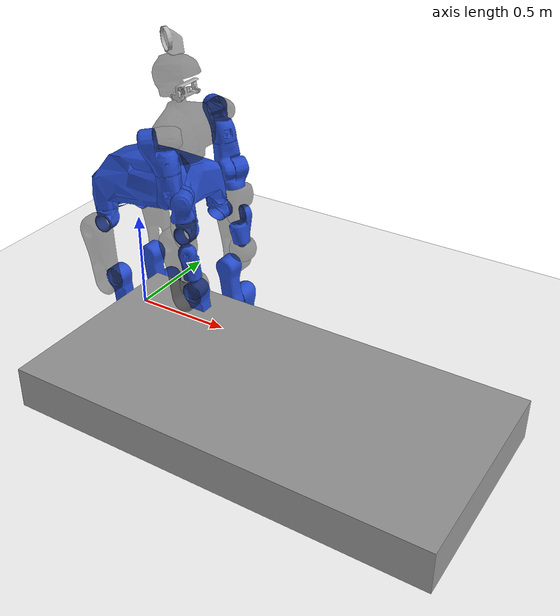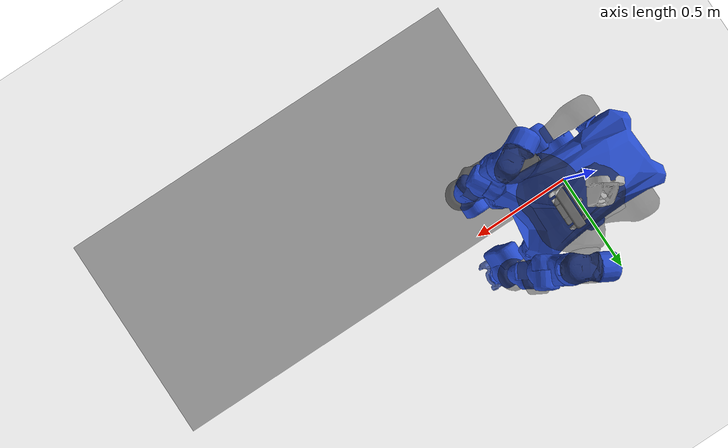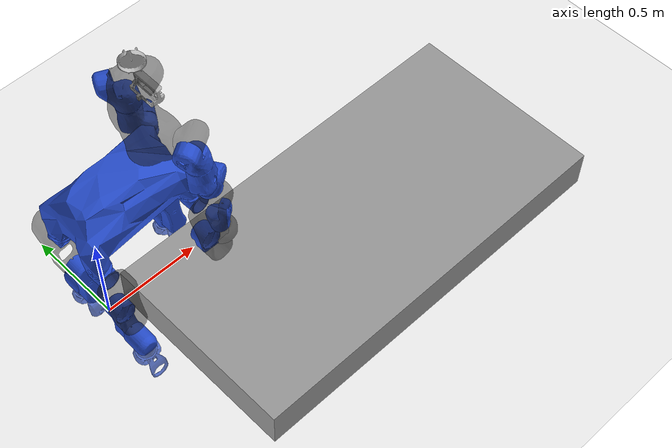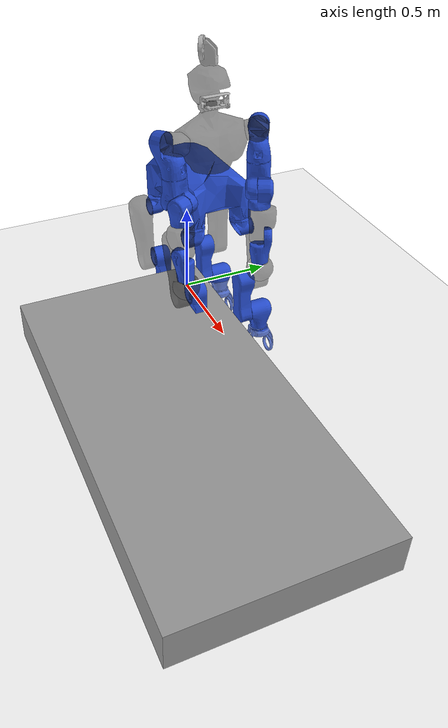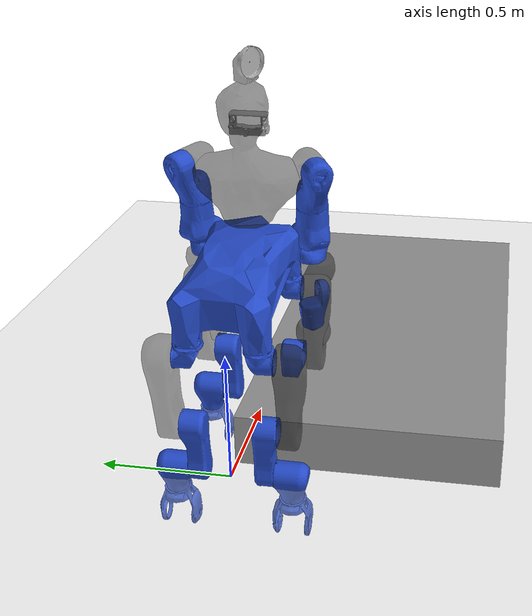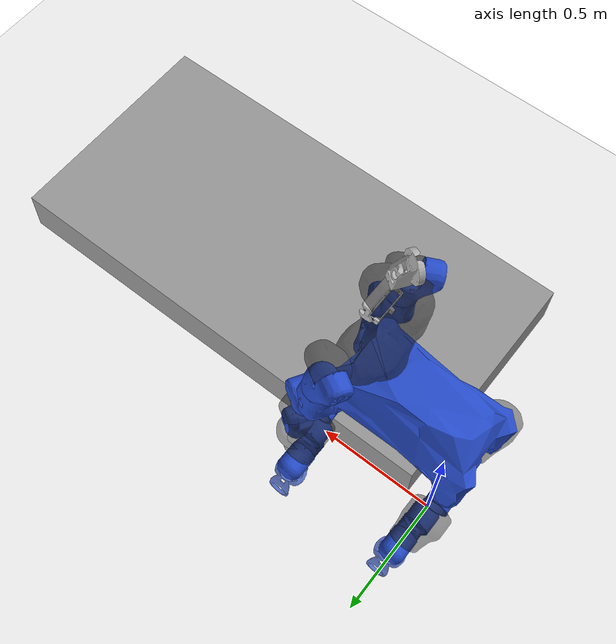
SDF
<sdf version="1.6">
 <world name="default">
  <plugin name="xbot2_clock" filename="libxbot2_gz_clock.so"/>
  <gravity>0 0 -9.81</gravity>
  <model name="ground_plane">
   <static>1</static>
   <link name="link">
    <collision name="collision">
     <geometry><plane><normal>0 0 1</normal><size>100 100</size></plane></geometry>
     <surface><friction><ode><mu>1</mu><mu2>1</mu2></ode></friction></surface>
    </collision>
    <visual name="visual">
     <cast_shadows>0</cast_shadows>
     <geometry><plane><normal>0 0 1</normal><size>100 100</size></plane></geometry>
     <material>
      <script><uri>file://media/materials/scripts/gazebo.material</uri><name>Gazebo/Grey</name></script>
     </material>
    </visual>
   </link>
  </model>
  <model name="unit_box">
   <pose>1.09537 -0.49391 0.1 0 -0 0</pose>
   <link name="link">
    <inertial>
     <mass>1000</mass>
     <inertia><ixx>100</ixx><ixy>0</ixy><ixz>0</ixz><iyy>100</iyy><iyz>0</iyz><izz>166</izz></inertia>
    </inertial>
    <collision name="collision"><geometry><box><size>2 1 0.2</size></box></geometry></collision>
    <visual name="visual">
     <geometry><box><size>2 1 0.2</size></box></geometry>
     <material>
      <script><name>Gazebo/Grey</name><uri>file://media/materials/scripts/gazebo.material</uri></script>
     </material>
    </visual>
    <kinematic>1</kinematic>
   </link>
  </model>
  <light name="sun" type="directional">
   <pose>0 0 10 0 -0 0</pose>
   <diffuse>0.8 0.8 0.8 1</diffuse>
   <specular>0.2 0.2 0.2 1</specular>
   <attenuation>
    <range>1000</range>
    <constant>0.9</constant>
    <linear>0.01</linear>
    <quadratic>0.001</quadratic>
   </attenuation>
   <direction>-0.5 0.1 -0.9</direction>
  </light>
  <physics name="update_rate" default="0" type="ode">
   <real_time_update_rate>4000</real_time_update_rate>
   <max_step_size>0.00025</max_step_size>
   <max_contacts>5</max_contacts>
   <bullet>
    <solver><iters>100</iters><sor>1.55</sor><type>sequential_impulse</type></solver>
    <constraints>
     <contact_surface_layer>0.2</contact_surface_layer>
     <cfm>0.005</cfm>
     <erp>0.2</erp>
     <split_impulse>1</split_impulse>
     <split_impulse_penetration_threshold>-0.01</split_impulse_penetration_threshold>
    </constraints>
   </bullet>
   <ode>
    <solver>
     <iters>50</iters>
     <sor>1.2</sor>
     <type>quick</type>
     <use_dynamic_moi_rescaling>0</use_dynamic_moi_rescaling>
    </solver>
    <constraints>
     <contact_surface_layer>0.0002</contact_surface_layer>
     <contact_max_correcting_vel>500</contact_max_correcting_vel>
     <cfm>1e-06</cfm>
     <erp>0.3</erp>
    </constraints>
   </ode>
   <real_time_factor>1</real_time_factor>
  </physics>
  <magnetic_field>6e-06 2.3e-05 -4.2e-05</magnetic_field>
  <atmosphere type="adiabatic"/>
  <scene><ambient>0.4 0.4 0.4 1</ambient><background>0.7 0.7 0.7 1</background><shadows>1</shadows></scene>
  <audio><device>default</device></audio>
  <spherical_coordinates>
   <surface_model>EARTH_WGS84</surface_model>
   <latitude_deg>0</latitude_deg>
   <longitude_deg>0</longitude_deg>
   <elevation>0</elevation>
   <heading_deg>0</heading_deg>
  </spherical_coordinates>
  <model name="centauro">
   <link name="pelvis">
    <inertial>
     <pose>0.001389 -0.001599 0.063101 0 -0 0</pose>
     <mass>16.0976</mass>
     <inertia>
      <ixx>0.239126</ixx>
      <ixy>-0.00505413</ixy>
      <ixz>-0.0197461</ixz>
      <iyy>0.714301</iyy>
      <iyz>0.00021312</iyz>
      <izz>0.818704</izz>
     </inertia>
    </inertial>
    <collision name="pelvis_collision">
     <geometry>
      <mesh>
       <scale>0.001 0.001 0.001</scale>
       <uri>/home/ioannis/centauro_ws/src/iit-centauro-ros-pkg/centauro_urdf/meshes/simple/pelvis.stl</uri>
      </mesh>
     </geometry>
    </collision>
    <visual name="pelvis_visual">
     <geometry>
      <mesh>
       <scale>0.001 0.001 0.001</scale>
       <uri>/home/ioannis/centauro_ws/src/iit-centauro-ros-pkg/centauro_urdf/meshes/pelvis.stl</uri>
      </mesh>
     </geometry>
     <material>
      <script><name>Gazebo/LightBlueLaser</name><uri>file://media/materials/scripts/gazebo.material</uri></script>
     </material>
    </visual>
    <sensor name="imu_link" type="imu">
     <always_on>1</always_on>
     <update_rate>500</update_rate>
     <visualize>1</visualize>
     <topic>__default_topic__</topic>
     <pose>0.248316 0 0.015 0 -0 0</pose>
    </sensor>
   </link>
   <link name="hip1_1">
    <pose>0.25 0.125 -0.0566 -3.14159 -0 0.461416</pose>
    <inertial>
     <pose>0.010214 -0.018348 0.038091 0 -0 0</pose>
     <mass>1.91944</mass>
     <inertia>
      <ixx>0.00474396</ixx>
      <ixy>0.000574705</ixy>
      <ixz>-0.000378414</ixz>
      <iyy>0.00405519</iyy>
      <iyz>0.000740751</iyz>
      <izz>0.00341462</izz>
     </inertia>
    </inertial>
    <collision name="hip1_1_collision">
     <pose>0 0 0 0 -0 -2.21876</pose>
     <geometry>
      <mesh>
       <scale>0.001 0.001 0.001</scale>
       <uri>/home/ioannis/centauro_ws/src/iit-centauro-ros-pkg/centauro_urdf/meshes/simple/hip-yaw.stl</uri>
      </mesh>
     </geometry>
    </collision>
    <visual name="hip1_1_visual">
     <pose>0 0 0 0 -0 -2.21876</pose>
     <geometry>
      <mesh>
       <scale>0.001 0.001 0.001</scale>
       <uri>/home/ioannis/centauro_ws/src/iit-centauro-ros-pkg/centauro_urdf/meshes/hip-yaw.stl</uri>
      </mesh>
     </geometry>
     <material>
      <script><name>Gazebo/LightBlueLaser</name><uri>file://media/materials/scripts/gazebo.material</uri></script>
     </material>
    </visual>
   </link>
   <joint name="hip_yaw_1" type="revolute">
    <child>hip1_1</child>
    <parent>pelvis</parent>
    <axis>
     <xyz>-0 0 -1</xyz>
     <limit><lower>-2.03</lower><upper>2.51</upper><effort>304</effort><velocity>8.8</velocity></limit>
     <dynamics><spring_reference>0</spring_reference><spring_stiffness>0</spring_stiffness></dynamics>
     <use_parent_model_frame>1</use_parent_model_frame>
    </axis>
    <physics>
     <provide_feedback>1</provide_feedback>
     <ode>
      <provide_feedback>1</provide_feedback>
      <implicit_spring_damper>1</implicit_spring_damper>
      <cfm_damping>1</cfm_damping>
      <limit><cfm>0</cfm><erp>0.2</erp></limit>
     </ode>
    </physics>
   </joint>
   <link name="hip2_1">
    <pose>0.25 0.125 -0.1191 -1.5708 0 0</pose>
    <inertial>
     <pose>2.6e-05 0.181027 0.08567 0 -0 0</pose>
     <mass>2.72645</mass>
     <inertia>
      <ixx>0.0485187</ixx>
      <ixy>-4.11894e-05</ixy>
      <ixz>-1.68778e-05</ixz>
      <iyy>0.00424205</iyy>
      <iyz>0.00322432</iyz>
      <izz>0.0482558</izz>
     </inertia>
    </inertial>
    <collision name="hip2_1_collision">
     <geometry>
      <mesh>
       <scale>0.001 0.001 0.001</scale>
       <uri>/home/ioannis/centauro_ws/src/iit-centauro-ros-pkg/centauro_urdf/meshes/simple/hip-pitch.stl</uri>
      </mesh>
     </geometry>
    </collision>
    <visual name="hip2_1_visual">
     <geometry>
      <mesh>
       <scale>0.001 0.001 0.001</scale>
       <uri>/home/ioannis/centauro_ws/src/iit-centauro-ros-pkg/centauro_urdf/meshes/hip-pitch.stl</uri>
      </mesh>
     </geometry>
     <material>
      <script><name>Gazebo/BlackTransparent</name><uri>file://media/materials/scripts/gazebo.material</uri></script>
     </material>
    </visual>
   </link>
   <joint name="hip_pitch_1" type="revolute">
    <child>hip2_1</child>
    <parent>hip1_1</parent>
    <axis>
     <xyz>0 1 -0</xyz>
     <limit><lower>-2.0226</lower><upper>2.02748</upper><effort>304</effort><velocity>8.8</velocity></limit>
     <dynamics><spring_reference>0</spring_reference><spring_stiffness>0</spring_stiffness></dynamics>
     <use_parent_model_frame>1</use_parent_model_frame>
    </axis>
    <physics>
     <provide_feedback>1</provide_feedback>
     <ode>
      <provide_feedback>1</provide_feedback>
      <implicit_spring_damper>1</implicit_spring_damper>
      <cfm_damping>1</cfm_damping>
      <limit><cfm>0</cfm><erp>0.2</erp></limit>
     </ode>
    </physics>
   </joint>
   <link name="knee_1">
    <pose>0.25 0.1214 -0.4191 -1.57079 1.57079 3.14159</pose>
    <inertial>
     <pose>0.108817 0.000109 -0.022639 0 -0 0</pose>
     <mass>1.93568</mass>
     <inertia>
      <ixx>0.00305342</ixx>
      <ixy>-4.22079e-05</ixy>
      <ixz>0.00136793</ixz>
      <iyy>0.0196033</iyy>
      <iyz>6.9941e-06</iyz>
      <izz>0.0198498</izz>
     </inertia>
    </inertial>
    <collision name="knee_1_collision">
     <geometry>
      <mesh>
       <scale>0.001 0.001 0.001</scale>
       <uri>/home/ioannis/centauro_ws/src/iit-centauro-ros-pkg/centauro_urdf/meshes/simple/knee.stl</uri>
      </mesh>
     </geometry>
    </collision>
    <visual name="knee_1_visual">
     <geometry>
      <mesh>
       <scale>0.001 0.001 0.001</scale>
       <uri>/home/ioannis/centauro_ws/src/iit-centauro-ros-pkg/centauro_urdf/meshes/knee.stl</uri>
      </mesh>
     </geometry>
     <material>
      <script><name>Gazebo/LightBlueLaser</name><uri>file://media/materials/scripts/gazebo.material</uri></script>
     </material>
    </visual>
   </link>
   <joint name="knee_pitch_1" type="revolute">
    <child>knee_1</child>
    <parent>hip2_1</parent>
    <axis>
     <xyz>-0 -1 0</xyz>
     <limit><lower>-2.4056</lower><upper>2.3994</upper><effort>304</effort><velocity>8.8</velocity></limit>
     <dynamics><spring_reference>0</spring_reference><spring_stiffness>0</spring_stiffness></dynamics>
     <use_parent_model_frame>1</use_parent_model_frame>
    </axis>
    <physics>
     <provide_feedback>1</provide_feedback>
     <ode>
      <provide_feedback>1</provide_feedback>
      <implicit_spring_damper>1</implicit_spring_damper>
      <cfm_damping>1</cfm_damping>
      <limit><cfm>0</cfm><erp>0.2</erp></limit>
     </ode>
    </physics>
   </joint>
   <link name="ankle1_1">
    <pose>0.25 0.22155 -0.6191 1.57079 1.57079 3.14159</pose>
    <inertial>
     <pose>0.032137 9.7e-05 -0.004422 0 -0 0</pose>
     <mass>1.23807</mass>
     <inertia>
      <ixx>0.00156105</ixx>
      <ixy>3.30597e-05</ixy>
      <ixz>-0.000131417</ixz>
      <iyy>0.00374232</iyy>
      <iyz>-2.12589e-05</iyz>
      <izz>0.00383124</izz>
     </inertia>
    </inertial>
    <collision name="ankle1_1_collision">
     <geometry>
      <mesh>
       <scale>0.001 0.001 0.001</scale>
       <uri>/home/ioannis/centauro_ws/src/iit-centauro-ros-pkg/centauro_urdf/meshes/simple/ankle-pitch.stl</uri>
      </mesh>
     </geometry>
    </collision>
    <visual name="ankle1_1_visual">
     <geometry>
      <mesh>
       <scale>0.001 0.001 0.001</scale>
       <uri>/home/ioannis/centauro_ws/src/iit-centauro-ros-pkg/centauro_urdf/meshes/ankle-pitch.stl</uri>
      </mesh>
     </geometry>
     <material>
      <script><name>Gazebo/LightBlueLaser</name><uri>file://media/materials/scripts/gazebo.material</uri></script>
     </material>
    </visual>
   </link>
   <joint name="ankle_pitch_1" type="revolute">
    <child>ankle1_1</child>
    <parent>knee_1</parent>
    <axis>
     <xyz>0 1 -0</xyz>
     <limit><lower>-2.4056</lower><upper>2.3184</upper><effort>147</effort><velocity>8.1</velocity></limit>
     <dynamics><spring_reference>0</spring_reference><spring_stiffness>0</spring_stiffness></dynamics>
     <use_parent_model_frame>1</use_parent_model_frame>
    </axis>
    <physics>
     <provide_feedback>1</provide_feedback>
     <ode>
      <provide_feedback>1</provide_feedback>
      <implicit_spring_damper>1</implicit_spring_damper>
      <cfm_damping>1</cfm_damping>
      <limit><cfm>0</cfm><erp>0.2</erp></limit>
     </ode>
    </physics>
   </joint>
   <link name="ankle2_1">
    <pose>0.25 0.22155 -0.6191 3.14159 -0 3.14159</pose>
    <inertial>
     <pose>0.000444 0.000439 0.193921 0 -0 0</pose>
     <mass>1.15659</mass>
     <inertia>
      <ixx>0.00490195</ixx>
      <ixy>4.3032e-06</ixy>
      <ixz>3.46491e-05</ixz>
      <iyy>0.00387242</iyy>
      <iyz>1.7099e-05</iyz>
      <izz>0.00217832</izz>
     </inertia>
    </inertial>
    <collision name="ankle2_1_collision">
     <geometry>
      <mesh>
       <scale>0.001 0.001 0.001</scale>
       <uri>/home/ioannis/centauro_ws/src/iit-centauro-ros-pkg/centauro_urdf/meshes/simple/ankle-yaw.stl</uri>
      </mesh>
     </geometry>
    </collision>
    <visual name="ankle2_1_visual">
     <geometry>
      <mesh>
       <scale>0.001 0.001 0.001</scale>
       <uri>/home/ioannis/centauro_ws/src/iit-centauro-ros-pkg/centauro_urdf/meshes/ankle-yaw.stl</uri>
      </mesh>
     </geometry>
     <material>
      <script><name>Gazebo/LightBlueLaser</name><uri>file://media/materials/scripts/gazebo.material</uri></script>
     </material>
    </visual>
   </link>
   <joint name="ankle_yaw_1" type="revolute">
    <child>ankle2_1</child>
    <parent>ankle1_1</parent>
    <axis>
     <xyz>0 0 -1</xyz>
     <limit><lower>-2.5626</lower><upper>2.5384</upper><effort>35</effort><velocity>20</velocity></limit>
     <dynamics><spring_reference>0</spring_reference><spring_stiffness>0</spring_stiffness></dynamics>
     <use_parent_model_frame>1</use_parent_model_frame>
    </axis>
    <physics>
     <provide_feedback>1</provide_feedback>
     <ode>
      <provide_feedback>1</provide_feedback>
      <implicit_spring_damper>1</implicit_spring_damper>
      <cfm_damping>1</cfm_damping>
      <limit><cfm>0</cfm><erp>0.2</erp></limit>
     </ode>
    </physics>
   </joint>
   <link name="wheel_1">
    <pose>0.25 0.2224 -0.85645 -1.5708 -0 -0</pose>
    <inertial>
     <pose>0 0 0.002427 0 -0 0</pose>
     <mass>1.7289</mass>
     <inertia>
      <ixx>0.00468643</ixx>
      <ixy>0</ixy>
      <ixz>0</ixz>
      <iyy>0.00467135</iyy>
      <iyz>0</iyz>
      <izz>0.0053126</izz>
     </inertia>
    </inertial>
    <collision name="wheel_1_collision">
     <geometry><cylinder><length>0.06</length><radius>0.078</radius></cylinder></geometry>
     <surface>
      <friction>
       <ode><mu>0.5</mu><mu2>0.5</mu2></ode>
       <bullet><friction>0.5</friction><friction2>0.5</friction2></bullet>
      </friction>
      <contact>
       <ode><kp>2.1e+06</kp><kd>1</kd><max_vel>100</max_vel></ode>
       <bullet>
        <soft_cfm>0.007</soft_cfm>
        <soft_erp>0.25</soft_erp>
        <kp>1e+06</kp>
        <kd>5</kd>
        <split_impulse>1</split_impulse>
        <split_impulse_penetration_threshold>-0.01</split_impulse_penetration_threshold>
       </bullet>
      </contact>
     </surface>
    </collision>
    <visual name="wheel_1_visual">
     <geometry>
      <mesh>
       <scale>0.001 0.001 0.001</scale>
       <uri>/home/ioannis/centauro_ws/src/iit-centauro-ros-pkg/centauro_urdf/meshes/wheel.stl</uri>
      </mesh>
     </geometry>
     <material>
      <script><name>Gazebo/BlackTransparent</name><uri>file://media/materials/scripts/gazebo.material</uri></script>
     </material>
    </visual>
   </link>
   <joint name="j_wheel_1" type="revolute">
    <child>wheel_1</child>
    <parent>ankle2_1</parent>
    <axis>
     <xyz>0 1 -0</xyz>
     <limit><lower>-1e+16</lower><upper>1e+16</upper></limit>
     <dynamics><spring_reference>0</spring_reference><spring_stiffness>0</spring_stiffness></dynamics>
     <use_parent_model_frame>1</use_parent_model_frame>
    </axis>
    <physics>
     <provide_feedback>1</provide_feedback>
     <ode>
      <provide_feedback>1</provide_feedback>
      <implicit_spring_damper>1</implicit_spring_damper>
      <cfm_damping>1</cfm_damping>
      <limit><cfm>0</cfm><erp>0.2</erp></limit>
     </ode>
    </physics>
   </joint>
   <link name="hip1_2">
    <pose>0.25 -0.125 -0.0566 -3.14159 -0 -0.461416</pose>
    <inertial>
     <pose>0.010214 0.018348 0.038091 0 -0 0</pose>
     <mass>1.91944</mass>
     <inertia>
      <ixx>0.00474396</ixx>
      <ixy>-0.000574705</ixy>
      <ixz>-0.000378414</ixz>
      <iyy>0.00405519</iyy>
      <iyz>-0.000740751</iyz>
      <izz>0.00341462</izz>
     </inertia>
    </inertial>
    <collision name="hip1_2_collision">
     <geometry>
      <mesh>
       <scale>0.001 0.001 0.001</scale>
       <uri>/home/ioannis/centauro_ws/src/iit-centauro-ros-pkg/centauro_urdf/meshes/simple/hip-yaw.stl</uri>
      </mesh>
     </geometry>
    </collision>
    <visual name="hip1_2_visual">
     <geometry>
      <mesh>
       <scale>0.001 0.001 0.001</scale>
       <uri>/home/ioannis/centauro_ws/src/iit-centauro-ros-pkg/centauro_urdf/meshes/hip-yaw.stl</uri>
      </mesh>
     </geometry>
     <material>
      <script><name>Gazebo/LightBlueLaser</name><uri>file://media/materials/scripts/gazebo.material</uri></script>
     </material>
    </visual>
   </link>
   <joint name="hip_yaw_2" type="revolute">
    <child>hip1_2</child>
    <parent>pelvis</parent>
    <axis>
     <xyz>0 0 -1</xyz>
     <limit><lower>-2.51</lower><upper>2.03</upper><effort>304</effort><velocity>8.8</velocity></limit>
     <dynamics><spring_reference>0</spring_reference><spring_stiffness>0</spring_stiffness></dynamics>
     <use_parent_model_frame>1</use_parent_model_frame>
    </axis>
    <physics>
     <provide_feedback>1</provide_feedback>
     <ode>
      <provide_feedback>1</provide_feedback>
      <implicit_spring_damper>1</implicit_spring_damper>
      <cfm_damping>1</cfm_damping>
      <limit><cfm>0</cfm><erp>0.2</erp></limit>
     </ode>
    </physics>
   </joint>
   <link name="hip2_2">
    <pose>0.25 -0.125 -0.1191 -1.5708 -0 -3.14159</pose>
    <inertial>
     <pose>2.6e-05 0.181027 0.08567 0 -0 0</pose>
     <mass>2.72645</mass>
     <inertia>
      <ixx>0.0485187</ixx>
      <ixy>-4.11894e-05</ixy>
      <ixz>-1.68778e-05</ixz>
      <iyy>0.00424205</iyy>
      <iyz>0.00322432</iyz>
      <izz>0.0482558</izz>
     </inertia>
    </inertial>
    <collision name="hip2_2_collision">
     <geometry>
      <mesh>
       <scale>0.001 0.001 0.001</scale>
       <uri>/home/ioannis/centauro_ws/src/iit-centauro-ros-pkg/centauro_urdf/meshes/simple/hip-pitch.stl</uri>
      </mesh>
     </geometry>
    </collision>
    <visual name="hip2_2_visual">
     <geometry>
      <mesh>
       <scale>0.001 0.001 0.001</scale>
       <uri>/home/ioannis/centauro_ws/src/iit-centauro-ros-pkg/centauro_urdf/meshes/hip-pitch.stl</uri>
      </mesh>
     </geometry>
     <material>
      <script><name>Gazebo/BlackTransparent</name><uri>file://media/materials/scripts/gazebo.material</uri></script>
     </material>
    </visual>
   </link>
   <joint name="hip_pitch_2" type="revolute">
    <child>hip2_2</child>
    <parent>hip1_2</parent>
    <axis>
     <xyz>0 -1 -0</xyz>
     <limit><lower>-2.0156</lower><upper>2.0354</upper><effort>304</effort><velocity>8.8</velocity></limit>
     <dynamics><spring_reference>0</spring_reference><spring_stiffness>0</spring_stiffness></dynamics>
     <use_parent_model_frame>1</use_parent_model_frame>
    </axis>
    <physics>
     <provide_feedback>1</provide_feedback>
     <ode>
      <provide_feedback>1</provide_feedback>
      <implicit_spring_damper>1</implicit_spring_damper>
      <cfm_damping>1</cfm_damping>
      <limit><cfm>0</cfm><erp>0.2</erp></limit>
     </ode>
    </physics>
   </joint>
   <link name="knee_2">
    <pose>0.25 -0.1214 -0.4191 1.57079 1.57079 3.14159</pose>
    <inertial>
     <pose>0.108817 0.000109 -0.022639 0 -0 0</pose>
     <mass>1.93568</mass>
     <inertia>
      <ixx>0.00305342</ixx>
      <ixy>-4.22079e-05</ixy>
      <ixz>0.00136793</ixz>
      <iyy>0.0196033</iyy>
      <iyz>6.9941e-06</iyz>
      <izz>0.0198498</izz>
     </inertia>
    </inertial>
    <collision name="knee_2_collision">
     <geometry>
      <mesh>
       <scale>0.001 0.001 0.001</scale>
       <uri>/home/ioannis/centauro_ws/src/iit-centauro-ros-pkg/centauro_urdf/meshes/simple/knee.stl</uri>
      </mesh>
     </geometry>
    </collision>
    <visual name="knee_2_visual">
     <geometry>
      <mesh>
       <scale>0.001 0.001 0.001</scale>
       <uri>/home/ioannis/centauro_ws/src/iit-centauro-ros-pkg/centauro_urdf/meshes/knee.stl</uri>
      </mesh>
     </geometry>
     <material>
      <script><name>Gazebo/LightBlueLaser</name><uri>file://media/materials/scripts/gazebo.material</uri></script>
     </material>
    </visual>
   </link>
   <joint name="knee_pitch_2" type="revolute">
    <child>knee_2</child>
    <parent>hip2_2</parent>
    <axis>
     <xyz>-0 1 0</xyz>
     <limit><lower>-2.4006</lower><upper>2.4034</upper><effort>304</effort><velocity>8.8</velocity></limit>
     <dynamics><spring_reference>0</spring_reference><spring_stiffness>0</spring_stiffness></dynamics>
     <use_parent_model_frame>1</use_parent_model_frame>
    </axis>
    <physics>
     <provide_feedback>1</provide_feedback>
     <ode>
      <provide_feedback>1</provide_feedback>
      <implicit_spring_damper>1</implicit_spring_damper>
      <cfm_damping>1</cfm_damping>
      <limit><cfm>0</cfm><erp>0.2</erp></limit>
     </ode>
    </physics>
   </joint>
   <link name="ankle1_2">
    <pose>0.25 -0.22155 -0.6191 -1.57079 1.57079 3.14159</pose>
    <inertial>
     <pose>0.032137 9.7e-05 -0.004422 0 -0 0</pose>
     <mass>1.23807</mass>
     <inertia>
      <ixx>0.00156105</ixx>
      <ixy>3.30597e-05</ixy>
      <ixz>-0.000131417</ixz>
      <iyy>0.00374232</iyy>
      <iyz>-2.12589e-05</iyz>
      <izz>0.00383124</izz>
     </inertia>
    </inertial>
    <collision name="ankle1_2_collision">
     <geometry>
      <mesh>
       <scale>0.001 0.001 0.001</scale>
       <uri>/home/ioannis/centauro_ws/src/iit-centauro-ros-pkg/centauro_urdf/meshes/simple/ankle-pitch.stl</uri>
      </mesh>
     </geometry>
    </collision>
    <visual name="ankle1_2_visual">
     <geometry>
      <mesh>
       <scale>0.001 0.001 0.001</scale>
       <uri>/home/ioannis/centauro_ws/src/iit-centauro-ros-pkg/centauro_urdf/meshes/ankle-pitch.stl</uri>
      </mesh>
     </geometry>
     <material>
      <script><name>Gazebo/LightBlueLaser</name><uri>file://media/materials/scripts/gazebo.material</uri></script>
     </material>
    </visual>
   </link>
   <joint name="ankle_pitch_2" type="revolute">
    <child>ankle1_2</child>
    <parent>knee_2</parent>
    <axis>
     <xyz>0 -1 -0</xyz>
     <limit><lower>-2.3266</lower><upper>2.3914</upper><effort>147</effort><velocity>8.1</velocity></limit>
     <dynamics><spring_reference>0</spring_reference><spring_stiffness>0</spring_stiffness></dynamics>
     <use_parent_model_frame>1</use_parent_model_frame>
    </axis>
    <physics>
     <provide_feedback>1</provide_feedback>
     <ode>
      <provide_feedback>1</provide_feedback>
      <implicit_spring_damper>1</implicit_spring_damper>
      <cfm_damping>1</cfm_damping>
      <limit><cfm>0</cfm><erp>0.2</erp></limit>
     </ode>
    </physics>
   </joint>
   <link name="ankle2_2">
    <pose>0.25 -0.22155 -0.6191 -3.14159 0 0</pose>
    <inertial>
     <pose>0.000444 0.000439 0.193921 0 -0 0</pose>
     <mass>1.15659</mass>
     <inertia>
      <ixx>0.00490195</ixx>
      <ixy>4.3032e-06</ixy>
      <ixz>3.46491e-05</ixz>
      <iyy>0.00387242</iyy>
      <iyz>1.7099e-05</iyz>
      <izz>0.00217832</izz>
     </inertia>
    </inertial>
    <collision name="ankle2_2_collision">
     <geometry>
      <mesh>
       <scale>0.001 0.001 0.001</scale>
       <uri>/home/ioannis/centauro_ws/src/iit-centauro-ros-pkg/centauro_urdf/meshes/simple/ankle-yaw.stl</uri>
      </mesh>
     </geometry>
    </collision>
    <visual name="ankle2_2_visual">
     <geometry>
      <mesh>
       <scale>0.001 0.001 0.001</scale>
       <uri>/home/ioannis/centauro_ws/src/iit-centauro-ros-pkg/centauro_urdf/meshes/ankle-yaw.stl</uri>
      </mesh>
     </geometry>
     <material>
      <script><name>Gazebo/LightBlueLaser</name><uri>file://media/materials/scripts/gazebo.material</uri></script>
     </material>
    </visual>
   </link>
   <joint name="ankle_yaw_2" type="revolute">
    <child>ankle2_2</child>
    <parent>ankle1_2</parent>
    <axis>
     <xyz>-0 0 -1</xyz>
     <limit><lower>-2.5546</lower><upper>2.5484</upper><effort>35</effort><velocity>20</velocity></limit>
     <dynamics><spring_reference>0</spring_reference><spring_stiffness>0</spring_stiffness></dynamics>
     <use_parent_model_frame>1</use_parent_model_frame>
    </axis>
    <physics>
     <provide_feedback>1</provide_feedback>
     <ode>
      <provide_feedback>1</provide_feedback>
      <implicit_spring_damper>1</implicit_spring_damper>
      <cfm_damping>1</cfm_damping>
      <limit><cfm>0</cfm><erp>0.2</erp></limit>
     </ode>
    </physics>
   </joint>
   <link name="wheel_2">
    <pose>0.25 -0.2224 -0.85645 -1.5708 -0 -3.14159</pose>
    <inertial>
     <pose>0 0 0.002427 0 -0 0</pose>
     <mass>1.7289</mass>
     <inertia>
      <ixx>0.00468643</ixx>
      <ixy>0</ixy>
      <ixz>0</ixz>
      <iyy>0.00467135</iyy>
      <iyz>0</iyz>
      <izz>0.0053126</izz>
     </inertia>
    </inertial>
    <collision name="wheel_2_collision">
     <geometry><cylinder><length>0.06</length><radius>0.078</radius></cylinder></geometry>
     <surface>
      <friction>
       <ode><mu>0.5</mu><mu2>0.5</mu2></ode>
       <bullet><friction>0.5</friction><friction2>0.5</friction2></bullet>
      </friction>
      <contact>
       <ode><kp>2.1e+06</kp><kd>1</kd><max_vel>100</max_vel></ode>
       <bullet>
        <soft_cfm>0.007</soft_cfm>
        <soft_erp>0.25</soft_erp>
        <kp>1e+06</kp>
        <kd>5</kd>
        <split_impulse>1</split_impulse>
        <split_impulse_penetration_threshold>-0.01</split_impulse_penetration_threshold>
       </bullet>
      </contact>
     </surface>
    </collision>
    <visual name="wheel_2_visual">
     <geometry>
      <mesh>
       <scale>0.001 0.001 0.001</scale>
       <uri>/home/ioannis/centauro_ws/src/iit-centauro-ros-pkg/centauro_urdf/meshes/wheel.stl</uri>
      </mesh>
     </geometry>
     <material>
      <script><name>Gazebo/BlackTransparent</name><uri>file://media/materials/scripts/gazebo.material</uri></script>
     </material>
    </visual>
   </link>
   <joint name="j_wheel_2" type="revolute">
    <child>wheel_2</child>
    <parent>ankle2_2</parent>
    <axis>
     <xyz>0 -1 -0</xyz>
     <limit><lower>-1e+16</lower><upper>1e+16</upper></limit>
     <dynamics><spring_reference>0</spring_reference><spring_stiffness>0</spring_stiffness></dynamics>
     <use_parent_model_frame>1</use_parent_model_frame>
    </axis>
    <physics>
     <provide_feedback>1</provide_feedback>
     <ode>
      <provide_feedback>1</provide_feedback>
      <implicit_spring_damper>1</implicit_spring_damper>
      <cfm_damping>1</cfm_damping>
      <limit><cfm>0</cfm><erp>0.2</erp></limit>
     </ode>
    </physics>
   </joint>
   <link name="hip1_3">
    <pose>-0.25 0.125 -0.0566 -3.14159 -0 2.68018</pose>
    <inertial>
     <pose>0.010214 0.018348 0.038091 0 -0 0</pose>
     <mass>1.91944</mass>
     <inertia>
      <ixx>0.00474396</ixx>
      <ixy>-0.000574705</ixy>
      <ixz>-0.000378414</ixz>
      <iyy>0.00405519</iyy>
      <iyz>-0.000740751</iyz>
      <izz>0.00341462</izz>
     </inertia>
    </inertial>
    <collision name="hip1_3_collision">
     <geometry>
      <mesh>
       <scale>0.001 0.001 0.001</scale>
       <uri>/home/ioannis/centauro_ws/src/iit-centauro-ros-pkg/centauro_urdf/meshes/simple/hip-yaw.stl</uri>
      </mesh>
     </geometry>
    </collision>
    <visual name="hip1_3_visual">
     <geometry>
      <mesh>
       <scale>0.001 0.001 0.001</scale>
       <uri>/home/ioannis/centauro_ws/src/iit-centauro-ros-pkg/centauro_urdf/meshes/hip-yaw.stl</uri>
      </mesh>
     </geometry>
     <material>
      <script><name>Gazebo/LightBlueLaser</name><uri>file://media/materials/scripts/gazebo.material</uri></script>
     </material>
    </visual>
   </link>
   <joint name="hip_yaw_3" type="revolute">
    <child>hip1_3</child>
    <parent>pelvis</parent>
    <axis>
     <xyz>-0 -0 -1</xyz>
     <limit><lower>-2.51</lower><upper>2.03</upper><effort>304</effort><velocity>8.8</velocity></limit>
     <dynamics><spring_reference>0</spring_reference><spring_stiffness>0</spring_stiffness></dynamics>
     <use_parent_model_frame>1</use_parent_model_frame>
    </axis>
    <physics>
     <provide_feedback>1</provide_feedback>
     <ode>
      <provide_feedback>1</provide_feedback>
      <implicit_spring_damper>1</implicit_spring_damper>
      <cfm_damping>1</cfm_damping>
      <limit><cfm>0</cfm><erp>0.2</erp></limit>
     </ode>
    </physics>
   </joint>
   <link name="hip2_3">
    <pose>-0.25 0.125 -0.1191 -1.5708 0 0</pose>
    <inertial>
     <pose>2.6e-05 0.181027 0.08567 0 -0 0</pose>
     <mass>2.72645</mass>
     <inertia>
      <ixx>0.0485187</ixx>
      <ixy>-4.11894e-05</ixy>
      <ixz>-1.68778e-05</ixz>
      <iyy>0.00424205</iyy>
      <iyz>0.00322432</iyz>
      <izz>0.0482558</izz>
     </inertia>
    </inertial>
    <collision name="hip2_3_collision">
     <geometry>
      <mesh>
       <scale>0.001 0.001 0.001</scale>
       <uri>/home/ioannis/centauro_ws/src/iit-centauro-ros-pkg/centauro_urdf/meshes/simple/hip-pitch.stl</uri>
      </mesh>
     </geometry>
    </collision>
    <visual name="hip2_3_visual">
     <geometry>
      <mesh>
       <scale>0.001 0.001 0.001</scale>
       <uri>/home/ioannis/centauro_ws/src/iit-centauro-ros-pkg/centauro_urdf/meshes/hip-pitch.stl</uri>
      </mesh>
     </geometry>
     <material>
      <script><name>Gazebo/BlackTransparent</name><uri>file://media/materials/scripts/gazebo.material</uri></script>
     </material>
    </visual>
   </link>
   <joint name="hip_pitch_3" type="revolute">
    <child>hip2_3</child>
    <parent>hip1_3</parent>
    <axis>
     <xyz>-0 1 -0</xyz>
     <limit><lower>-2.0126</lower><upper>2.0384</upper><effort>304</effort><velocity>8.8</velocity></limit>
     <dynamics><spring_reference>0</spring_reference><spring_stiffness>0</spring_stiffness></dynamics>
     <use_parent_model_frame>1</use_parent_model_frame>
    </axis>
    <physics>
     <provide_feedback>1</provide_feedback>
     <ode>
      <provide_feedback>1</provide_feedback>
      <implicit_spring_damper>1</implicit_spring_damper>
      <cfm_damping>1</cfm_damping>
      <limit><cfm>0</cfm><erp>0.2</erp></limit>
     </ode>
    </physics>
   </joint>
   <link name="knee_3">
    <pose>-0.25 0.1214 -0.4191 -1.57079 1.57079 3.14159</pose>
    <inertial>
     <pose>0.108817 0.000109 -0.022639 0 -0 0</pose>
     <mass>1.93568</mass>
     <inertia>
      <ixx>0.00305342</ixx>
      <ixy>-4.22079e-05</ixy>
      <ixz>0.00136793</ixz>
      <iyy>0.0196033</iyy>
      <iyz>6.9941e-06</iyz>
      <izz>0.0198498</izz>
     </inertia>
    </inertial>
    <collision name="knee_3_collision">
     <geometry>
      <mesh>
       <scale>0.001 0.001 0.001</scale>
       <uri>/home/ioannis/centauro_ws/src/iit-centauro-ros-pkg/centauro_urdf/meshes/simple/knee.stl</uri>
      </mesh>
     </geometry>
    </collision>
    <visual name="knee_3_visual">
     <geometry>
      <mesh>
       <scale>0.001 0.001 0.001</scale>
       <uri>/home/ioannis/centauro_ws/src/iit-centauro-ros-pkg/centauro_urdf/meshes/knee.stl</uri>
      </mesh>
     </geometry>
     <material>
      <script><name>Gazebo/LightBlueLaser</name><uri>file://media/materials/scripts/gazebo.material</uri></script>
     </material>
    </visual>
   </link>
   <joint name="knee_pitch_3" type="revolute">
    <child>knee_3</child>
    <parent>hip2_3</parent>
    <axis>
     <xyz>-0 -1 0</xyz>
     <limit><lower>-2.4056</lower><upper>2.4064</upper><effort>304</effort><velocity>8.8</velocity></limit>
     <dynamics><spring_reference>0</spring_reference><spring_stiffness>0</spring_stiffness></dynamics>
     <use_parent_model_frame>1</use_parent_model_frame>
    </axis>
    <physics>
     <provide_feedback>1</provide_feedback>
     <ode>
      <provide_feedback>1</provide_feedback>
      <implicit_spring_damper>1</implicit_spring_damper>
      <cfm_damping>1</cfm_damping>
      <limit><cfm>0</cfm><erp>0.2</erp></limit>
     </ode>
    </physics>
   </joint>
   <link name="ankle1_3">
    <pose>-0.25 0.22155 -0.6191 1.57079 1.57079 3.14159</pose>
    <inertial>
     <pose>0.032137 9.7e-05 -0.004422 0 -0 0</pose>
     <mass>1.23807</mass>
     <inertia>
      <ixx>0.00156105</ixx>
      <ixy>3.30597e-05</ixy>
      <ixz>-0.000131417</ixz>
      <iyy>0.00374232</iyy>
      <iyz>-2.12589e-05</iyz>
      <izz>0.00383124</izz>
     </inertia>
    </inertial>
    <collision name="ankle1_3_collision">
     <geometry>
      <mesh>
       <scale>0.001 0.001 0.001</scale>
       <uri>/home/ioannis/centauro_ws/src/iit-centauro-ros-pkg/centauro_urdf/meshes/simple/ankle-pitch.stl</uri>
      </mesh>
     </geometry>
    </collision>
    <visual name="ankle1_3_visual">
     <geometry>
      <mesh>
       <scale>0.001 0.001 0.001</scale>
       <uri>/home/ioannis/centauro_ws/src/iit-centauro-ros-pkg/centauro_urdf/meshes/ankle-pitch.stl</uri>
      </mesh>
     </geometry>
     <material>
      <script><name>Gazebo/LightBlueLaser</name><uri>file://media/materials/scripts/gazebo.material</uri></script>
     </material>
    </visual>
   </link>
   <joint name="ankle_pitch_3" type="revolute">
    <child>ankle1_3</child>
    <parent>knee_3</parent>
    <axis>
     <xyz>0 1 -0</xyz>
     <limit><lower>-2.4696</lower><upper>2.4464</upper><effort>147</effort><velocity>8.1</velocity></limit>
     <dynamics><spring_reference>0</spring_reference><spring_stiffness>0</spring_stiffness></dynamics>
     <use_parent_model_frame>1</use_parent_model_frame>
    </axis>
    <physics>
     <provide_feedback>1</provide_feedback>
     <ode>
      <provide_feedback>1</provide_feedback>
      <implicit_spring_damper>1</implicit_spring_damper>
      <cfm_damping>1</cfm_damping>
      <limit><cfm>0</cfm><erp>0.2</erp></limit>
     </ode>
    </physics>
   </joint>
   <link name="ankle2_3">
    <pose>-0.25 0.22155 -0.6191 -3.14159 -0 3.14159</pose>
    <inertial>
     <pose>0.000444 0.000439 0.193921 0 -0 0</pose>
     <mass>1.15659</mass>
     <inertia>
      <ixx>0.00490195</ixx>
      <ixy>4.3032e-06</ixy>
      <ixz>3.46491e-05</ixz>
      <iyy>0.00387242</iyy>
      <iyz>1.7099e-05</iyz>
      <izz>0.00217832</izz>
     </inertia>
    </inertial>
    <collision name="ankle2_3_collision">
     <geometry>
      <mesh>
       <scale>0.001 0.001 0.001</scale>
       <uri>/home/ioannis/centauro_ws/src/iit-centauro-ros-pkg/centauro_urdf/meshes/simple/ankle-yaw.stl</uri>
      </mesh>
     </geometry>
    </collision>
    <visual name="ankle2_3_visual">
     <geometry>
      <mesh>
       <scale>0.001 0.001 0.001</scale>
       <uri>/home/ioannis/centauro_ws/src/iit-centauro-ros-pkg/centauro_urdf/meshes/ankle-yaw.stl</uri>
      </mesh>
     </geometry>
     <material>
      <script><name>Gazebo/LightBlueLaser</name><uri>file://media/materials/scripts/gazebo.material</uri></script>
     </material>
    </visual>
   </link>
   <joint name="ankle_yaw_3" type="revolute">
    <child>ankle2_3</child>
    <parent>ankle1_3</parent>
    <axis>
     <xyz>0 -0 -1</xyz>
     <limit><lower>-2.5606</lower><upper>2.5454</upper><effort>35</effort><velocity>20</velocity></limit>
     <dynamics><spring_reference>0</spring_reference><spring_stiffness>0</spring_stiffness></dynamics>
     <use_parent_model_frame>1</use_parent_model_frame>
    </axis>
    <physics>
     <provide_feedback>1</provide_feedback>
     <ode>
      <provide_feedback>1</provide_feedback>
      <implicit_spring_damper>1</implicit_spring_damper>
      <cfm_damping>1</cfm_damping>
      <limit><cfm>0</cfm><erp>0.2</erp></limit>
     </ode>
    </physics>
   </joint>
   <link name="wheel_3">
    <pose>-0.25 0.2224 -0.85645 -1.5708 -0 -0</pose>
    <inertial>
     <pose>0 0 0.002427 0 -0 0</pose>
     <mass>1.7289</mass>
     <inertia>
      <ixx>0.00468643</ixx>
      <ixy>0</ixy>
      <ixz>0</ixz>
      <iyy>0.00467135</iyy>
      <iyz>0</iyz>
      <izz>0.0053126</izz>
     </inertia>
    </inertial>
    <collision name="wheel_3_collision">
     <geometry><cylinder><length>0.06</length><radius>0.078</radius></cylinder></geometry>
     <surface>
      <friction>
       <ode><mu>0.5</mu><mu2>0.5</mu2></ode>
       <bullet><friction>0.5</friction><friction2>0.5</friction2></bullet>
      </friction>
      <contact>
       <ode><kp>2.1e+06</kp><kd>1</kd><max_vel>100</max_vel></ode>
       <bullet>
        <soft_cfm>0.007</soft_cfm>
        <soft_erp>0.25</soft_erp>
        <kp>1e+06</kp>
        <kd>5</kd>
        <split_impulse>1</split_impulse>
        <split_impulse_penetration_threshold>-0.01</split_impulse_penetration_threshold>
       </bullet>
      </contact>
     </surface>
    </collision>
    <visual name="wheel_3_visual">
     <geometry>
      <mesh>
       <scale>0.001 0.001 0.001</scale>
       <uri>/home/ioannis/centauro_ws/src/iit-centauro-ros-pkg/centauro_urdf/meshes/wheel.stl</uri>
      </mesh>
     </geometry>
     <material>
      <script><name>Gazebo/BlackTransparent</name><uri>file://media/materials/scripts/gazebo.material</uri></script>
     </material>
    </visual>
   </link>
   <joint name="j_wheel_3" type="revolute">
    <child>wheel_3</child>
    <parent>ankle2_3</parent>
    <axis>
     <xyz>0 1 -0</xyz>
     <limit><lower>-1e+16</lower><upper>1e+16</upper></limit>
     <dynamics><spring_reference>0</spring_reference><spring_stiffness>0</spring_stiffness></dynamics>
     <use_parent_model_frame>1</use_parent_model_frame>
    </axis>
    <physics>
     <provide_feedback>1</provide_feedback>
     <ode>
      <provide_feedback>1</provide_feedback>
      <implicit_spring_damper>1</implicit_spring_damper>
      <cfm_damping>1</cfm_damping>
      <limit><cfm>0</cfm><erp>0.2</erp></limit>
     </ode>
    </physics>
   </joint>
   <link name="hip1_4">
    <pose>-0.25 -0.125 -0.0566 -3.14159 -0 -2.68018</pose>
    <inertial>
     <pose>0.010214 -0.018348 0.038091 0 -0 0</pose>
     <mass>1.91944</mass>
     <inertia>
      <ixx>0.00474396</ixx>
      <ixy>0.000574705</ixy>
      <ixz>-0.000378414</ixz>
      <iyy>0.00405519</iyy>
      <iyz>0.000740751</iyz>
      <izz>0.00341462</izz>
     </inertia>
    </inertial>
    <collision name="hip1_4_collision">
     <pose>0 0 0 0 -0 -2.21876</pose>
     <geometry>
      <mesh>
       <scale>0.001 0.001 0.001</scale>
       <uri>/home/ioannis/centauro_ws/src/iit-centauro-ros-pkg/centauro_urdf/meshes/simple/hip-yaw.stl</uri>
      </mesh>
     </geometry>
    </collision>
    <visual name="hip1_4_visual">
     <pose>0 0 0 0 -0 -2.21876</pose>
     <geometry>
      <mesh>
       <scale>0.001 0.001 0.001</scale>
       <uri>/home/ioannis/centauro_ws/src/iit-centauro-ros-pkg/centauro_urdf/meshes/hip-yaw.stl</uri>
      </mesh>
     </geometry>
     <material>
      <script><name>Gazebo/LightBlueLaser</name><uri>file://media/materials/scripts/gazebo.material</uri></script>
     </material>
    </visual>
   </link>
   <joint name="hip_yaw_4" type="revolute">
    <child>hip1_4</child>
    <parent>pelvis</parent>
    <axis>
     <xyz>0 -0 -1</xyz>
     <limit><lower>-2.03</lower><upper>2.51</upper><effort>304</effort><velocity>8.8</velocity></limit>
     <dynamics><spring_reference>0</spring_reference><spring_stiffness>0</spring_stiffness></dynamics>
     <use_parent_model_frame>1</use_parent_model_frame>
    </axis>
    <physics>
     <provide_feedback>1</provide_feedback>
     <ode>
      <provide_feedback>1</provide_feedback>
      <implicit_spring_damper>1</implicit_spring_damper>
      <cfm_damping>1</cfm_damping>
      <limit><cfm>0</cfm><erp>0.2</erp></limit>
     </ode>
    </physics>
   </joint>
   <link name="hip2_4">
    <pose>-0.25 -0.125 -0.1191 -1.5708 -0 -3.14159</pose>
    <inertial>
     <pose>2.6e-05 0.181027 0.08567 0 -0 0</pose>
     <mass>2.72645</mass>
     <inertia>
      <ixx>0.0485187</ixx>
      <ixy>-4.11894e-05</ixy>
      <ixz>-1.68778e-05</ixz>
      <iyy>0.00424205</iyy>
      <iyz>0.00322432</iyz>
      <izz>0.0482558</izz>
     </inertia>
    </inertial>
    <collision name="hip2_4_collision">
     <geometry>
      <mesh>
       <scale>0.001 0.001 0.001</scale>
       <uri>/home/ioannis/centauro_ws/src/iit-centauro-ros-pkg/centauro_urdf/meshes/simple/hip-pitch.stl</uri>
      </mesh>
     </geometry>
    </collision>
    <visual name="hip2_4_visual">
     <geometry>
      <mesh>
       <scale>0.001 0.001 0.001</scale>
       <uri>/home/ioannis/centauro_ws/src/iit-centauro-ros-pkg/centauro_urdf/meshes/hip-pitch.stl</uri>
      </mesh>
     </geometry>
     <material>
      <script><name>Gazebo/BlackTransparent</name><uri>file://media/materials/scripts/gazebo.material</uri></script>
     </material>
    </visual>
   </link>
   <joint name="hip_pitch_4" type="revolute">
    <child>hip2_4</child>
    <parent>hip1_4</parent>
    <axis>
     <xyz>0 -1 -0</xyz>
     <limit><lower>-2.0326</lower><upper>2.0524</upper><effort>304</effort><velocity>8.8</velocity></limit>
     <dynamics><spring_reference>0</spring_reference><spring_stiffness>0</spring_stiffness></dynamics>
     <use_parent_model_frame>1</use_parent_model_frame>
    </axis>
    <physics>
     <provide_feedback>1</provide_feedback>
     <ode>
      <provide_feedback>1</provide_feedback>
      <implicit_spring_damper>1</implicit_spring_damper>
      <cfm_damping>1</cfm_damping>
      <limit><cfm>0</cfm><erp>0.2</erp></limit>
     </ode>
    </physics>
   </joint>
   <link name="knee_4">
    <pose>-0.25 -0.1214 -0.4191 1.57079 1.57079 3.14159</pose>
    <inertial>
     <pose>0.108817 0.000109 -0.022639 0 -0 0</pose>
     <mass>1.93568</mass>
     <inertia>
      <ixx>0.00305342</ixx>
      <ixy>-4.22079e-05</ixy>
      <ixz>0.00136793</ixz>
      <iyy>0.0196033</iyy>
      <iyz>6.9941e-06</iyz>
      <izz>0.0198498</izz>
     </inertia>
    </inertial>
    <collision name="knee_4_collision">
     <geometry>
      <mesh>
       <scale>0.001 0.001 0.001</scale>
       <uri>/home/ioannis/centauro_ws/src/iit-centauro-ros-pkg/centauro_urdf/meshes/simple/knee.stl</uri>
      </mesh>
     </geometry>
    </collision>
    <visual name="knee_4_visual">
     <geometry>
      <mesh>
       <scale>0.001 0.001 0.001</scale>
       <uri>/home/ioannis/centauro_ws/src/iit-centauro-ros-pkg/centauro_urdf/meshes/knee.stl</uri>
      </mesh>
     </geometry>
     <material>
      <script><name>Gazebo/LightBlueLaser</name><uri>file://media/materials/scripts/gazebo.material</uri></script>
     </material>
    </visual>
   </link>
   <joint name="knee_pitch_4" type="revolute">
    <child>knee_4</child>
    <parent>hip2_4</parent>
    <axis>
     <xyz>0 1 0</xyz>
     <limit><lower>-2.4176</lower><upper>2.3884</upper><effort>304</effort><velocity>8.8</velocity></limit>
     <dynamics><spring_reference>0</spring_reference><spring_stiffness>0</spring_stiffness></dynamics>
     <use_parent_model_frame>1</use_parent_model_frame>
    </axis>
    <physics>
     <provide_feedback>1</provide_feedback>
     <ode>
      <provide_feedback>1</provide_feedback>
      <implicit_spring_damper>1</implicit_spring_damper>
      <cfm_damping>1</cfm_damping>
      <limit><cfm>0</cfm><erp>0.2</erp></limit>
     </ode>
    </physics>
   </joint>
   <link name="ankle1_4">
    <pose>-0.25 -0.22155 -0.6191 -1.57079 1.57079 3.14159</pose>
    <inertial>
     <pose>0.032137 9.7e-05 -0.004422 0 -0 0</pose>
     <mass>1.23807</mass>
     <inertia>
      <ixx>0.00156105</ixx>
      <ixy>3.30597e-05</ixy>
      <ixz>-0.000131417</ixz>
      <iyy>0.00374232</iyy>
      <iyz>-2.12589e-05</iyz>
      <izz>0.00383124</izz>
     </inertia>
    </inertial>
    <collision name="ankle1_4_collision">
     <geometry>
      <mesh>
       <scale>0.001 0.001 0.001</scale>
       <uri>/home/ioannis/centauro_ws/src/iit-centauro-ros-pkg/centauro_urdf/meshes/simple/ankle-pitch.stl</uri>
      </mesh>
     </geometry>
    </collision>
    <visual name="ankle1_4_visual">
     <geometry>
      <mesh>
       <scale>0.001 0.001 0.001</scale>
       <uri>/home/ioannis/centauro_ws/src/iit-centauro-ros-pkg/centauro_urdf/meshes/ankle-pitch.stl</uri>
      </mesh>
     </geometry>
     <material>
      <script><name>Gazebo/LightBlueLaser</name><uri>file://media/materials/scripts/gazebo.material</uri></script>
     </material>
    </visual>
   </link>
   <joint name="ankle_pitch_4" type="revolute">
    <child>ankle1_4</child>
    <parent>knee_4</parent>
    <axis>
     <xyz>-0 -1 -0</xyz>
     <limit><lower>-2.3426</lower><upper>2.3934</upper><effort>147</effort><velocity>8.1</velocity></limit>
     <dynamics><spring_reference>0</spring_reference><spring_stiffness>0</spring_stiffness></dynamics>
     <use_parent_model_frame>1</use_parent_model_frame>
    </axis>
    <physics>
     <provide_feedback>1</provide_feedback>
     <ode>
      <provide_feedback>1</provide_feedback>
      <implicit_spring_damper>1</implicit_spring_damper>
      <cfm_damping>1</cfm_damping>
      <limit><cfm>0</cfm><erp>0.2</erp></limit>
     </ode>
    </physics>
   </joint>
   <link name="ankle2_4">
    <pose>-0.25 -0.22155 -0.6191 3.14159 -0 0</pose>
    <inertial>
     <pose>0.000444 0.000439 0.193921 0 -0 0</pose>
     <mass>1.15659</mass>
     <inertia>
      <ixx>0.00490195</ixx>
      <ixy>4.3032e-06</ixy>
      <ixz>3.46491e-05</ixz>
      <iyy>0.00387242</iyy>
      <iyz>1.7099e-05</iyz>
      <izz>0.00217832</izz>
     </inertia>
    </inertial>
    <collision name="ankle2_4_collision">
     <geometry>
      <mesh>
       <scale>0.001 0.001 0.001</scale>
       <uri>/home/ioannis/centauro_ws/src/iit-centauro-ros-pkg/centauro_urdf/meshes/simple/ankle-yaw.stl</uri>
      </mesh>
     </geometry>
    </collision>
    <visual name="ankle2_4_visual">
     <geometry>
      <mesh>
       <scale>0.001 0.001 0.001</scale>
       <uri>/home/ioannis/centauro_ws/src/iit-centauro-ros-pkg/centauro_urdf/meshes/ankle-yaw.stl</uri>
      </mesh>
     </geometry>
     <material>
      <script><name>Gazebo/LightBlueLaser</name><uri>file://media/materials/scripts/gazebo.material</uri></script>
     </material>
    </visual>
   </link>
   <joint name="ankle_yaw_4" type="revolute">
    <child>ankle2_4</child>
    <parent>ankle1_4</parent>
    <axis>
     <xyz>-0 -0 -1</xyz>
     <limit><lower>-2.6046</lower><upper>2.5514</upper><effort>35</effort><velocity>20</velocity></limit>
     <dynamics><spring_reference>0</spring_reference><spring_stiffness>0</spring_stiffness></dynamics>
     <use_parent_model_frame>1</use_parent_model_frame>
    </axis>
    <physics>
     <provide_feedback>1</provide_feedback>
     <ode>
      <provide_feedback>1</provide_feedback>
      <implicit_spring_damper>1</implicit_spring_damper>
      <cfm_damping>1</cfm_damping>
      <limit><cfm>0</cfm><erp>0.2</erp></limit>
     </ode>
    </physics>
   </joint>
   <link name="wheel_4">
    <pose>-0.25 -0.2224 -0.85645 -1.5708 -0 3.14159</pose>
    <inertial>
     <pose>0 0 0.002427 0 -0 0</pose>
     <mass>1.7289</mass>
     <inertia>
      <ixx>0.00468643</ixx>
      <ixy>0</ixy>
      <ixz>0</ixz>
      <iyy>0.00467135</iyy>
      <iyz>0</iyz>
      <izz>0.0053126</izz>
     </inertia>
    </inertial>
    <collision name="wheel_4_collision">
     <geometry><cylinder><length>0.06</length><radius>0.078</radius></cylinder></geometry>
     <surface>
      <friction>
       <ode><mu>0.5</mu><mu2>0.5</mu2></ode>
       <bullet><friction>0.5</friction><friction2>0.5</friction2></bullet>
      </friction>
      <contact>
       <ode><kp>2.1e+06</kp><kd>1</kd><max_vel>100</max_vel></ode>
       <bullet>
        <soft_cfm>0.007</soft_cfm>
        <soft_erp>0.25</soft_erp>
        <kp>1e+06</kp>
        <kd>5</kd>
        <split_impulse>1</split_impulse>
        <split_impulse_penetration_threshold>-0.01</split_impulse_penetration_threshold>
       </bullet>
      </contact>
     </surface>
    </collision>
    <visual name="wheel_4_visual">
     <geometry>
      <mesh>
       <scale>0.001 0.001 0.001</scale>
       <uri>/home/ioannis/centauro_ws/src/iit-centauro-ros-pkg/centauro_urdf/meshes/wheel.stl</uri>
      </mesh>
     </geometry>
     <material>
      <script><name>Gazebo/BlackTransparent</name><uri>file://media/materials/scripts/gazebo.material</uri></script>
     </material>
    </visual>
   </link>
   <joint name="j_wheel_4" type="revolute">
    <child>wheel_4</child>
    <parent>ankle2_4</parent>
    <axis>
     <xyz>-0 -1 -0</xyz>
     <limit><lower>-1e+16</lower><upper>1e+16</upper></limit>
     <dynamics><spring_reference>0</spring_reference><spring_stiffness>0</spring_stiffness></dynamics>
     <use_parent_model_frame>1</use_parent_model_frame>
    </axis>
    <physics>
     <provide_feedback>1</provide_feedback>
     <ode>
      <provide_feedback>1</provide_feedback>
      <implicit_spring_damper>1</implicit_spring_damper>
      <cfm_damping>1</cfm_damping>
      <limit><cfm>0</cfm><erp>0.2</erp></limit>
     </ode>
    </physics>
   </joint>
   <link name="torso_2">
    <pose>0.2 0 0.256 0 -0 0</pose>
    <inertial>
     <pose>-0.019498 0.004532 0.137683 0 -0 0</pose>
     <mass>11.4927</mass>
     <inertia>
      <ixx>0.0636434</ixx>
      <ixy>8.939e-05</ixy>
      <ixz>-0.00086873</ixz>
      <iyy>0.0268023</iyy>
      <iyz>-4.657e-05</iyz>
      <izz>0.0474301</izz>
     </inertia>
    </inertial>
    <collision name="torso_2_collision">
     <geometry>
      <mesh>
       <scale>0.001 0.001 0.001</scale>
       <uri>/home/ioannis/centauro_ws/src/iit-centauro-ros-pkg/centauro_urdf/meshes/simple/link1.stl</uri>
      </mesh>
     </geometry>
    </collision>
    <visual name="torso_2_visual">
     <geometry>
      <mesh>
       <scale>0.001 0.001 0.001</scale>
       <uri>/home/ioannis/centauro_ws/src/iit-centauro-ros-pkg/centauro_urdf/meshes/link1.stl</uri>
      </mesh>
     </geometry>
     <material>
      <script><name>Gazebo/BlackTransparent</name><uri>file://media/materials/scripts/gazebo.material</uri></script>
     </material>
    </visual>
   </link>
   <joint name="torso_yaw" type="revolute">
    <child>torso_2</child>
    <parent>pelvis</parent>
    <axis>
     <xyz>0 0 1</xyz>
     <limit><lower>-2.618</lower><upper>2.618</upper><effort>147</effort><velocity>5.7</velocity></limit>
     <dynamics><spring_reference>0</spring_reference><spring_stiffness>0</spring_stiffness></dynamics>
     <use_parent_model_frame>1</use_parent_model_frame>
    </axis>
    <physics>
     <provide_feedback>1</provide_feedback>
     <ode>
      <provide_feedback>1</provide_feedback>
      <implicit_spring_damper>1</implicit_spring_damper>
      <cfm_damping>1</cfm_damping>
      <limit><cfm>0</cfm><erp>0.2</erp></limit>
     </ode>
    </physics>
   </joint>
   <link name="arm1_1">
    <pose>0.245748 0.169137 0.372626 0.174533 -0 -0.523599</pose>
    <inertial>
     <pose>-0.007446 0.034108 0.00011 0 -0 0</pose>
     <mass>1.96287</mass>
     <inertia>
      <ixx>0.00535477</ixx>
      <ixy>0.000364289</ixy>
      <ixz>1.50896e-05</ixz>
      <iyy>0.00339233</iyy>
      <iyz>5.56923e-05</iyz>
      <izz>0.00689214</izz>
     </inertia>
    </inertial>
    <collision name="arm1_1_collision">
     <geometry>
      <mesh>
       <scale>0.001 -0.001 0.001</scale>
       <uri>/home/ioannis/centauro_ws/src/iit-centauro-ros-pkg/centauro_urdf/meshes/simple/ShoulderPitch.STL</uri>
      </mesh>
     </geometry>
    </collision>
    <visual name="arm1_1_visual">
     <geometry>
      <mesh>
       <scale>0.001 -0.001 0.001</scale>
       <uri>/home/ioannis/centauro_ws/src/iit-centauro-ros-pkg/centauro_urdf/meshes/ShoulderPitch.STL</uri>
      </mesh>
     </geometry>
     <material>
      <script><name>Gazebo/BlackTransparent</name><uri>file://media/materials/scripts/gazebo.material</uri></script>
     </material>
    </visual>
   </link>
   <joint name="j_arm1_1" type="revolute">
    <child>arm1_1</child>
    <parent>torso_2</parent>
    <axis>
     <xyz>0.492404 0.852869 0.173648</xyz>
     <limit><lower>-3.312</lower><upper>1.615</upper><effort>147</effort><velocity>3.86</velocity></limit>
     <dynamics><spring_reference>0</spring_reference><spring_stiffness>0</spring_stiffness></dynamics>
     <use_parent_model_frame>1</use_parent_model_frame>
    </axis>
    <physics>
     <provide_feedback>1</provide_feedback>
     <ode>
      <provide_feedback>1</provide_feedback>
      <implicit_spring_damper>1</implicit_spring_damper>
      <cfm_damping>1</cfm_damping>
      <limit><cfm>0</cfm><erp>0.2</erp></limit>
     </ode>
    </physics>
   </joint>
   <link name="arm1_2">
    <pose>0.198204 0.26709 0.383392 0 0 -0.523599</pose>
    <inertial>
     <pose>0.058142 5.7e-05 -0.077478 0 -0 0</pose>
     <mass>1.85958</mass>
     <inertia>
      <ixx>0.0137766</ixx>
      <ixy>3.77887e-05</ixy>
      <ixz>0.00376902</ixz>
      <iyy>0.0156775</iyy>
      <iyz>-9.48935e-06</iyz>
      <izz>0.00463177</izz>
     </inertia>
    </inertial>
    <collision name="arm1_2_collision">
     <geometry>
      <mesh>
       <scale>0.001 -0.001 0.001</scale>
       <uri>/home/ioannis/centauro_ws/src/iit-centauro-ros-pkg/centauro_urdf/meshes/simple/ShoulderRoll.STL</uri>
      </mesh>
     </geometry>
    </collision>
    <visual name="arm1_2_visual">
     <geometry>
      <mesh>
       <scale>0.001 -0.001 0.001</scale>
       <uri>/home/ioannis/centauro_ws/src/iit-centauro-ros-pkg/centauro_urdf/meshes/ShoulderRoll.STL</uri>
      </mesh>
     </geometry>
     <material>
      <script><name>Gazebo/LightBlueLaser</name><uri>file://media/materials/scripts/gazebo.material</uri></script>
     </material>
    </visual>
   </link>
   <joint name="j_arm1_2" type="revolute">
    <child>arm1_2</child>
    <parent>arm1_1</parent>
    <axis>
     <xyz>0.866025 -0.5 -0</xyz>
     <limit><lower>0.02</lower><upper>3.431</upper><effort>147</effort><velocity>3.86</velocity></limit>
     <dynamics><spring_reference>0</spring_reference><spring_stiffness>0</spring_stiffness></dynamics>
     <use_parent_model_frame>1</use_parent_model_frame>
    </axis>
    <physics>
     <provide_feedback>1</provide_feedback>
     <ode>
      <provide_feedback>1</provide_feedback>
      <implicit_spring_damper>1</implicit_spring_damper>
      <cfm_damping>1</cfm_damping>
      <limit><cfm>0</cfm><erp>0.2</erp></limit>
     </ode>
    </physics>
   </joint>
   <link name="arm1_3">
    <pose>0.276277 0.222015 0.165242 0 0 -0.523599</pose>
    <inertial>
     <pose>0.014625 0.000817 -0.028334 0 -0 0</pose>
     <mass>1.66781</mass>
     <inertia>
      <ixx>0.00644804</ixx>
      <ixy>-0.000156391</ixy>
      <ixz>0.00122054</ixz>
      <iyy>0.00733721</iyy>
      <iyz>8.99415e-05</iyz>
      <izz>0.00367384</izz>
     </inertia>
    </inertial>
    <collision name="arm1_3_collision">
     <geometry>
      <mesh>
       <scale>0.001 -0.001 0.001</scale>
       <uri>/home/ioannis/centauro_ws/src/iit-centauro-ros-pkg/centauro_urdf/meshes/simple/ShoulderYaw.STL</uri>
      </mesh>
     </geometry>
    </collision>
    <visual name="arm1_3_visual">
     <geometry>
      <mesh>
       <scale>0.001 -0.001 0.001</scale>
       <uri>/home/ioannis/centauro_ws/src/iit-centauro-ros-pkg/centauro_urdf/meshes/ShoulderYaw.STL</uri>
      </mesh>
     </geometry>
     <material>
      <script><name>Gazebo/LightBlueLaser</name><uri>file://media/materials/scripts/gazebo.material</uri></script>
     </material>
    </visual>
   </link>
   <joint name="j_arm1_3" type="revolute">
    <child>arm1_3</child>
    <parent>arm1_2</parent>
    <axis>
     <xyz>-0 -0 1</xyz>
     <limit><lower>-2.552</lower><upper>2.566</upper><effort>147</effort><velocity>6.06</velocity></limit>
     <dynamics><spring_reference>0</spring_reference><spring_stiffness>0</spring_stiffness></dynamics>
     <use_parent_model_frame>1</use_parent_model_frame>
    </axis>
    <physics>
     <provide_feedback>1</provide_feedback>
     <ode>
      <provide_feedback>1</provide_feedback>
      <implicit_spring_damper>1</implicit_spring_damper>
      <cfm_damping>1</cfm_damping>
      <limit><cfm>0</cfm><erp>0.2</erp></limit>
     </ode>
    </physics>
   </joint>
   <link name="arm1_4">
    <pose>0.342823 0.247276 0.091242 0 0 -0.523599</pose>
    <inertial>
     <pose>-0.007683 -0.040302 -0.043493 0 -0 0</pose>
     <mass>1.31573</mass>
     <inertia>
      <ixx>0.00433039</ixx>
      <ixy>-0.000117374</ixy>
      <ixz>-0.000419232</ixz>
      <iyy>0.00385399</iyy>
      <iyz>-0.00079573</iyz>
      <izz>0.00175947</izz>
     </inertia>
    </inertial>
    <collision name="arm1_4_collision">
     <geometry>
      <mesh>
       <scale>0.001 -0.001 0.001</scale>
       <uri>/home/ioannis/centauro_ws/src/iit-centauro-ros-pkg/centauro_urdf/meshes/simple/Elbow.STL</uri>
      </mesh>
     </geometry>
    </collision>
    <visual name="arm1_4_visual">
     <geometry>
      <mesh>
       <scale>0.001 -0.001 0.001</scale>
       <uri>/home/ioannis/centauro_ws/src/iit-centauro-ros-pkg/centauro_urdf/meshes/Elbow.STL</uri>
      </mesh>
     </geometry>
     <material>
      <script><name>Gazebo/LightBlueLaser</name><uri>file://media/materials/scripts/gazebo.material</uri></script>
     </material>
    </visual>
   </link>
   <joint name="j_arm1_4" type="revolute">
    <child>arm1_4</child>
    <parent>arm1_3</parent>
    <axis>
     <xyz>0.5 0.866025 0</xyz>
     <limit><lower>-2.465</lower><upper>0.28</upper><effort>147</effort><velocity>6.06</velocity></limit>
     <dynamics><spring_reference>0</spring_reference><spring_stiffness>0</spring_stiffness></dynamics>
     <use_parent_model_frame>1</use_parent_model_frame>
    </axis>
    <physics>
     <provide_feedback>1</provide_feedback>
     <ode>
      <provide_feedback>1</provide_feedback>
      <implicit_spring_damper>1</implicit_spring_damper>
      <cfm_damping>1</cfm_damping>
      <limit><cfm>0</cfm><erp>0.2</erp></limit>
     </ode>
    </physics>
   </joint>
   <link name="arm1_5">
    <pose>0.302257 0.207015 -0.003758 0 0 -0.523599</pose>
    <inertial>
     <pose>-0.000111 0.011591 -0.07816 0 -0 0</pose>
     <mass>1.49085</mass>
     <inertia>
      <ixx>0.00856921</ixx>
      <ixy>1.78563e-05</ixy>
      <ixz>1.93794e-05</ixz>
      <iyy>0.00774542</iyy>
      <iyz>-0.000328601</iyz>
      <izz>0.00274419</izz>
     </inertia>
    </inertial>
    <collision name="arm1_5_collision">
     <geometry>
      <mesh>
       <scale>0.001 -0.001 0.001</scale>
       <uri>/home/ioannis/centauro_ws/src/iit-centauro-ros-pkg/centauro_urdf/meshes/simple/Forearm.STL</uri>
      </mesh>
     </geometry>
    </collision>
    <visual name="arm1_5_visual">
     <geometry>
      <mesh>
       <scale>0.001 -0.001 0.001</scale>
       <uri>/home/ioannis/centauro_ws/src/iit-centauro-ros-pkg/centauro_urdf/meshes/Forearm.STL</uri>
      </mesh>
     </geometry>
     <material>
      <script><name>Gazebo/BlackTransparent</name><uri>file://media/materials/scripts/gazebo.material</uri></script>
     </material>
    </visual>
   </link>
   <joint name="j_arm1_5" type="revolute">
    <child>arm1_5</child>
    <parent>arm1_4</parent>
    <axis>
     <xyz>-0 -0 1</xyz>
     <limit><lower>-2.569</lower><upper>2.562</upper><effort>55</effort><velocity>11.72</velocity></limit>
     <dynamics><spring_reference>0</spring_reference><spring_stiffness>0</spring_stiffness></dynamics>
     <use_parent_model_frame>1</use_parent_model_frame>
    </axis>
    <physics>
     <provide_feedback>1</provide_feedback>
     <ode>
      <provide_feedback>1</provide_feedback>
      <implicit_spring_damper>1</implicit_spring_damper>
      <cfm_damping>1</cfm_damping>
      <limit><cfm>0</cfm><erp>0.2</erp></limit>
     </ode>
    </physics>
   </joint>
   <link name="arm1_6">
    <pose>0.326757 0.24945 -0.159758 0 0 -0.523599</pose>
    <inertial>
     <pose>-5e-06 -0.038014 -0.069927 0 -0 0</pose>
     <mass>1.12636</mass>
     <inertia>
      <ixx>0.00518718</ixx>
      <ixy>2.72444e-05</ixy>
      <ixz>2.28335e-06</ixz>
      <iyy>0.00480378</iyy>
      <iyz>-0.000721657</iyz>
      <izz>0.00127714</izz>
     </inertia>
    </inertial>
    <collision name="arm1_6_collision">
     <geometry>
      <mesh>
       <scale>0.001 -0.001 0.001</scale>
       <uri>/home/ioannis/centauro_ws/src/iit-centauro-ros-pkg/centauro_urdf/meshes/simple/ForearmPitch.STL</uri>
      </mesh>
     </geometry>
    </collision>
    <visual name="arm1_6_visual">
     <geometry>
      <mesh>
       <scale>0.001 -0.001 0.001</scale>
       <uri>/home/ioannis/centauro_ws/src/iit-centauro-ros-pkg/centauro_urdf/meshes/ForearmPitch.STL</uri>
      </mesh>
     </geometry>
     <material>
      <script><name>Gazebo/LightBlueLaser</name><uri>file://media/materials/scripts/gazebo.material</uri></script>
     </material>
    </visual>
   </link>
   <joint name="j_arm1_6" type="revolute">
    <child>arm1_6</child>
    <parent>arm1_5</parent>
    <axis>
     <xyz>0.5 0.866025 0</xyz>
     <limit><lower>-1.529</lower><upper>1.509</upper><effort>55</effort><velocity>11.72</velocity></limit>
     <dynamics><spring_reference>0</spring_reference><spring_stiffness>0</spring_stiffness></dynamics>
     <use_parent_model_frame>1</use_parent_model_frame>
    </axis>
    <physics>
     <provide_feedback>1</provide_feedback>
     <ode>
      <provide_feedback>1</provide_feedback>
      <implicit_spring_damper>1</implicit_spring_damper>
      <cfm_damping>1</cfm_damping>
      <limit><cfm>0</cfm><erp>0.2</erp></limit>
     </ode>
    </physics>
   </joint>
   <link name="arm1_7">
    <pose>0.302257 0.207015 -0.333758 0 0 -0.523599</pose>
    <inertial>
     <pose>9e-06 0.000541 0.01433 0 -0 0</pose>
     <mass>1.92794</mass>
     <inertia>
      <ixx>0.00316217</ixx>
      <ixy>2.68715e-06</ixy>
      <ixz>-9.8962e-07</ixz>
      <iyy>0.00313238</iyy>
      <iyz>6.27992e-05</iyz>
      <izz>0.00340412</izz>
     </inertia>
    </inertial>
    <collision name="arm1_7_collision">
     <geometry>
      <mesh>
       <scale>0.001 -0.001 0.001</scale>
       <uri>/home/ioannis/centauro_ws/src/iit-centauro-ros-pkg/centauro_urdf/meshes/simple/ForearmYaw.STL</uri>
      </mesh>
     </geometry>
    </collision>
    <collision name="arm1_7_fixed_joint_lump__ball1_collision_1">
     <geometry>
      <mesh>
       <scale>0.001 0.001 0.001</scale>
       <uri>/home/ioannis/centauro_ws/src/iit-centauro-ros-pkg/centauro_urdf/meshes/simple/BallHand.stl</uri>
      </mesh>
     </geometry>
    </collision>
    <visual name="arm1_7_visual">
     <geometry>
      <mesh>
       <scale>0.001 -0.001 0.001</scale>
       <uri>/home/ioannis/centauro_ws/src/iit-centauro-ros-pkg/centauro_urdf/meshes/ForearmYaw.STL</uri>
      </mesh>
     </geometry>
     <material>
      <script><name>Gazebo/LightBlueLaser</name><uri>file://media/materials/scripts/gazebo.material</uri></script>
     </material>
    </visual>
    <visual name="arm1_7_fixed_joint_lump__ball1_visual_1">
     <geometry>
      <mesh>
       <scale>0.001 0.001 0.001</scale>
       <uri>/home/ioannis/centauro_ws/src/iit-centauro-ros-pkg/centauro_urdf/meshes/BallHand.stl</uri>
      </mesh>
     </geometry>
     <material>
      <script><name>Gazebo/BlackTransparent</name><uri>file://media/materials/scripts/gazebo.material</uri></script>
     </material>
    </visual>
   </link>
   <joint name="j_arm1_7" type="revolute">
    <child>arm1_7</child>
    <parent>arm1_6</parent>
    <axis>
     <xyz>-0 -0 1</xyz>
     <limit><lower>-2.565</lower><upper>2.569</upper><effort>28.32</effort><velocity>20.35</velocity></limit>
     <dynamics><spring_reference>0</spring_reference><spring_stiffness>0</spring_stiffness></dynamics>
     <use_parent_model_frame>1</use_parent_model_frame>
    </axis>
    <physics>
     <provide_feedback>1</provide_feedback>
     <ode>
      <provide_feedback>1</provide_feedback>
      <implicit_spring_damper>1</implicit_spring_damper>
      <cfm_damping>1</cfm_damping>
      <limit><cfm>0</cfm><erp>0.2</erp></limit>
     </ode>
    </physics>
   </joint>
   <link name="arm2_1">
    <pose>0.245748 -0.169137 0.372626 -0.174533 -0 0.523599</pose>
    <inertial>
     <pose>-0.007446 -0.034108 0.00011 0 -0 0</pose>
     <mass>1.96287</mass>
     <inertia>
      <ixx>0.00535477</ixx>
      <ixy>-0.000364289</ixy>
      <ixz>1.50896e-05</ixz>
      <iyy>0.00339233</iyy>
      <iyz>-5.56923e-05</iyz>
      <izz>0.00689214</izz>
     </inertia>
    </inertial>
    <collision name="arm2_1_collision">
     <geometry>
      <mesh>
       <scale>0.001 0.001 0.001</scale>
       <uri>/home/ioannis/centauro_ws/src/iit-centauro-ros-pkg/centauro_urdf/meshes/simple/ShoulderPitch.STL</uri>
      </mesh>
     </geometry>
    </collision>
    <visual name="arm2_1_visual">
     <geometry>
      <mesh>
       <scale>0.001 0.001 0.001</scale>
       <uri>/home/ioannis/centauro_ws/src/iit-centauro-ros-pkg/centauro_urdf/meshes/ShoulderPitch.STL</uri>
      </mesh>
     </geometry>
     <material>
      <script><name>Gazebo/BlackTransparent</name><uri>file://media/materials/scripts/gazebo.material</uri></script>
     </material>
    </visual>
   </link>
   <joint name="j_arm2_1" type="revolute">
    <child>arm2_1</child>
    <parent>torso_2</parent>
    <axis>
     <xyz>-0.492404 0.852869 -0.173648</xyz>
     <limit><lower>-3.3458</lower><upper>1.6012</upper><effort>147</effort><velocity>3.86</velocity></limit>
     <dynamics><spring_reference>0</spring_reference><spring_stiffness>0</spring_stiffness></dynamics>
     <use_parent_model_frame>1</use_parent_model_frame>
    </axis>
    <physics>
     <provide_feedback>1</provide_feedback>
     <ode>
      <provide_feedback>1</provide_feedback>
      <implicit_spring_damper>1</implicit_spring_damper>
      <cfm_damping>1</cfm_damping>
      <limit><cfm>0</cfm><erp>0.2</erp></limit>
     </ode>
    </physics>
   </joint>
   <link name="arm2_2">
    <pose>0.198204 -0.26709 0.383392 0 -0 0.523599</pose>
    <inertial>
     <pose>0.058142 -5.7e-05 -0.077478 0 -0 0</pose>
     <mass>1.85958</mass>
     <inertia>
      <ixx>0.0137766</ixx>
      <ixy>-3.77887e-05</ixy>
      <ixz>0.00376902</ixz>
      <iyy>0.0156775</iyy>
      <iyz>9.48935e-06</iyz>
      <izz>0.00463177</izz>
     </inertia>
    </inertial>
    <collision name="arm2_2_collision">
     <geometry>
      <mesh>
       <scale>0.001 0.001 0.001</scale>
       <uri>/home/ioannis/centauro_ws/src/iit-centauro-ros-pkg/centauro_urdf/meshes/simple/ShoulderRoll.STL</uri>
      </mesh>
     </geometry>
    </collision>
    <visual name="arm2_2_visual">
     <geometry>
      <mesh>
       <scale>0.001 0.001 0.001</scale>
       <uri>/home/ioannis/centauro_ws/src/iit-centauro-ros-pkg/centauro_urdf/meshes/ShoulderRoll.STL</uri>
      </mesh>
     </geometry>
     <material>
      <script><name>Gazebo/LightBlueLaser</name><uri>file://media/materials/scripts/gazebo.material</uri></script>
     </material>
    </visual>
   </link>
   <joint name="j_arm2_2" type="revolute">
    <child>arm2_2</child>
    <parent>arm2_1</parent>
    <axis>
     <xyz>0.866025 0.5 -0</xyz>
     <limit><lower>-3.4258</lower><upper>-0.0138</upper><effort>147</effort><velocity>3.86</velocity></limit>
     <dynamics><spring_reference>0</spring_reference><spring_stiffness>0</spring_stiffness></dynamics>
     <use_parent_model_frame>1</use_parent_model_frame>
    </axis>
    <physics>
     <provide_feedback>1</provide_feedback>
     <ode>
      <provide_feedback>1</provide_feedback>
      <implicit_spring_damper>1</implicit_spring_damper>
      <cfm_damping>1</cfm_damping>
      <limit><cfm>0</cfm><erp>0.2</erp></limit>
     </ode>
    </physics>
   </joint>
   <link name="arm2_3">
    <pose>0.276277 -0.222015 0.165242 0 -0 0.523599</pose>
    <inertial>
     <pose>0.014625 -0.000817 -0.028334 0 -0 0</pose>
     <mass>1.66781</mass>
     <inertia>
      <ixx>0.00644804</ixx>
      <ixy>0.000156391</ixy>
      <ixz>0.00122054</ixz>
      <iyy>0.00733721</iyy>
      <iyz>-8.99415e-05</iyz>
      <izz>0.00367384</izz>
     </inertia>
    </inertial>
    <collision name="arm2_3_collision">
     <geometry>
      <mesh>
       <scale>0.001 0.001 0.001</scale>
       <uri>/home/ioannis/centauro_ws/src/iit-centauro-ros-pkg/centauro_urdf/meshes/simple/ShoulderYaw.STL</uri>
      </mesh>
     </geometry>
    </collision>
    <visual name="arm2_3_visual">
     <geometry>
      <mesh>
       <scale>0.001 0.001 0.001</scale>
       <uri>/home/ioannis/centauro_ws/src/iit-centauro-ros-pkg/centauro_urdf/meshes/ShoulderYaw.STL</uri>
      </mesh>
     </geometry>
     <material>
      <script><name>Gazebo/LightBlueLaser</name><uri>file://media/materials/scripts/gazebo.material</uri></script>
     </material>
    </visual>
   </link>
   <joint name="j_arm2_3" type="revolute">
    <child>arm2_3</child>
    <parent>arm2_2</parent>
    <axis>
     <xyz>-0 0 1</xyz>
     <limit><lower>-2.5614</lower><upper>2.5606</upper><effort>147</effort><velocity>6.06</velocity></limit>
     <dynamics><spring_reference>0</spring_reference><spring_stiffness>0</spring_stiffness></dynamics>
     <use_parent_model_frame>1</use_parent_model_frame>
    </axis>
    <physics>
     <provide_feedback>1</provide_feedback>
     <ode>
      <provide_feedback>1</provide_feedback>
      <implicit_spring_damper>1</implicit_spring_damper>
      <cfm_damping>1</cfm_damping>
      <limit><cfm>0</cfm><erp>0.2</erp></limit>
     </ode>
    </physics>
   </joint>
   <link name="arm2_4">
    <pose>0.342823 -0.247276 0.091242 0 -0 0.523599</pose>
    <inertial>
     <pose>-0.007683 0.040302 -0.043493 0 -0 0</pose>
     <mass>1.31573</mass>
     <inertia>
      <ixx>0.00433039</ixx>
      <ixy>0.000117374</ixy>
      <ixz>-0.000419232</ixz>
      <iyy>0.00385399</iyy>
      <iyz>0.00079573</iyz>
      <izz>0.00175947</izz>
     </inertia>
    </inertial>
    <collision name="arm2_4_collision">
     <geometry>
      <mesh>
       <scale>0.001 0.001 0.001</scale>
       <uri>/home/ioannis/centauro_ws/src/iit-centauro-ros-pkg/centauro_urdf/meshes/simple/Elbow.STL</uri>
      </mesh>
     </geometry>
    </collision>
    <visual name="arm2_4_visual">
     <geometry>
      <mesh>
       <scale>0.001 0.001 0.001</scale>
       <uri>/home/ioannis/centauro_ws/src/iit-centauro-ros-pkg/centauro_urdf/meshes/Elbow.STL</uri>
      </mesh>
     </geometry>
     <material>
      <script><name>Gazebo/LightBlueLaser</name><uri>file://media/materials/scripts/gazebo.material</uri></script>
     </material>
    </visual>
   </link>
   <joint name="j_arm2_4" type="revolute">
    <child>arm2_4</child>
    <parent>arm2_3</parent>
    <axis>
     <xyz>-0.5 0.866025 -0</xyz>
     <limit><lower>-2.4794</lower><upper>0.2886</upper><effort>147</effort><velocity>6.06</velocity></limit>
     <dynamics><spring_reference>0</spring_reference><spring_stiffness>0</spring_stiffness></dynamics>
     <use_parent_model_frame>1</use_parent_model_frame>
    </axis>
    <physics>
     <provide_feedback>1</provide_feedback>
     <ode>
      <provide_feedback>1</provide_feedback>
      <implicit_spring_damper>1</implicit_spring_damper>
      <cfm_damping>1</cfm_damping>
      <limit><cfm>0</cfm><erp>0.2</erp></limit>
     </ode>
    </physics>
   </joint>
   <link name="arm2_5">
    <pose>0.302257 -0.207015 -0.003758 0 -0 0.523599</pose>
    <inertial>
     <pose>-0.000111 -0.011591 -0.07816 0 -0 0</pose>
     <mass>1.49085</mass>
     <inertia>
      <ixx>0.00856921</ixx>
      <ixy>-1.78563e-05</ixy>
      <ixz>1.93794e-05</ixz>
      <iyy>0.00774542</iyy>
      <iyz>0.000328601</iyz>
      <izz>0.00274419</izz>
     </inertia>
    </inertial>
    <collision name="arm2_5_collision">
     <geometry>
      <mesh>
       <scale>0.001 0.001 0.001</scale>
       <uri>/home/ioannis/centauro_ws/src/iit-centauro-ros-pkg/centauro_urdf/meshes/simple/Forearm.STL</uri>
      </mesh>
     </geometry>
    </collision>
    <visual name="arm2_5_visual">
     <geometry>
      <mesh>
       <scale>0.001 0.001 0.001</scale>
       <uri>/home/ioannis/centauro_ws/src/iit-centauro-ros-pkg/centauro_urdf/meshes/Forearm.STL</uri>
      </mesh>
     </geometry>
     <material>
      <script><name>Gazebo/BlackTransparent</name><uri>file://media/materials/scripts/gazebo.material</uri></script>
     </material>
    </visual>
   </link>
   <joint name="j_arm2_5" type="revolute">
    <child>arm2_5</child>
    <parent>arm2_4</parent>
    <axis>
     <xyz>-0 0 1</xyz>
     <limit><lower>-2.5394</lower><upper>2.5546</upper><effort>55</effort><velocity>11.72</velocity></limit>
     <dynamics><spring_reference>0</spring_reference><spring_stiffness>0</spring_stiffness></dynamics>
     <use_parent_model_frame>1</use_parent_model_frame>
    </axis>
    <physics>
     <provide_feedback>1</provide_feedback>
     <ode>
      <provide_feedback>1</provide_feedback>
      <implicit_spring_damper>1</implicit_spring_damper>
      <cfm_damping>1</cfm_damping>
      <limit><cfm>0</cfm><erp>0.2</erp></limit>
     </ode>
    </physics>
   </joint>
   <link name="arm2_6">
    <pose>0.326757 -0.24945 -0.159758 0 -0 0.523599</pose>
    <inertial>
     <pose>-5e-06 0.038014 -0.069927 0 -0 0</pose>
     <mass>1.12636</mass>
     <inertia>
      <ixx>0.00518718</ixx>
      <ixy>-2.72444e-05</ixy>
      <ixz>2.28335e-06</ixz>
      <iyy>0.00480378</iyy>
      <iyz>0.000721657</iyz>
      <izz>0.00127714</izz>
     </inertia>
    </inertial>
    <collision name="arm2_6_collision">
     <geometry>
      <mesh>
       <scale>0.001 0.001 0.001</scale>
       <uri>/home/ioannis/centauro_ws/src/iit-centauro-ros-pkg/centauro_urdf/meshes/simple/ForearmPitch.STL</uri>
      </mesh>
     </geometry>
    </collision>
    <visual name="arm2_6_visual">
     <geometry>
      <mesh>
       <scale>0.001 0.001 0.001</scale>
       <uri>/home/ioannis/centauro_ws/src/iit-centauro-ros-pkg/centauro_urdf/meshes/ForearmPitch.STL</uri>
      </mesh>
     </geometry>
     <material>
      <script><name>Gazebo/LightBlueLaser</name><uri>file://media/materials/scripts/gazebo.material</uri></script>
     </material>
    </visual>
   </link>
   <joint name="j_arm2_6" type="revolute">
    <child>arm2_6</child>
    <parent>arm2_5</parent>
    <axis>
     <xyz>-0.5 0.866025 -0</xyz>
     <limit><lower>-1.5154</lower><upper>1.5156</upper><effort>55</effort><velocity>11.72</velocity></limit>
     <dynamics><spring_reference>0</spring_reference><spring_stiffness>0</spring_stiffness></dynamics>
     <use_parent_model_frame>1</use_parent_model_frame>
    </axis>
    <physics>
     <provide_feedback>1</provide_feedback>
     <ode>
      <provide_feedback>1</provide_feedback>
      <implicit_spring_damper>1</implicit_spring_damper>
      <cfm_damping>1</cfm_damping>
      <limit><cfm>0</cfm><erp>0.2</erp></limit>
     </ode>
    </physics>
   </joint>
   <link name="arm2_7">
    <pose>0.302257 -0.207015 -0.333758 0 -0 0.523599</pose>
    <inertial>
     <pose>9e-06 -0.000492 0.01433 0 -0 0</pose>
     <mass>1.92794</mass>
     <inertia>
      <ixx>0.00316227</ixx>
      <ixy>-2.10165e-06</ixy>
      <ixz>-9.8962e-07</ixz>
      <iyy>0.00313238</iyy>
      <iyz>-6.1733e-05</iyz>
      <izz>0.00340422</izz>
     </inertia>
    </inertial>
    <collision name="arm2_7_collision">
     <geometry>
      <mesh>
       <scale>0.001 0.001 0.001</scale>
       <uri>/home/ioannis/centauro_ws/src/iit-centauro-ros-pkg/centauro_urdf/meshes/simple/ForearmYaw.STL</uri>
      </mesh>
     </geometry>
    </collision>
    <collision name="arm2_7_fixed_joint_lump__ball2_collision_1">
     <geometry>
      <mesh>
       <scale>0.001 0.001 0.001</scale>
       <uri>/home/ioannis/centauro_ws/src/iit-centauro-ros-pkg/centauro_urdf/meshes/simple/BallHand.stl</uri>
      </mesh>
     </geometry>
    </collision>
    <visual name="arm2_7_visual">
     <geometry>
      <mesh>
       <scale>0.001 0.001 0.001</scale>
       <uri>/home/ioannis/centauro_ws/src/iit-centauro-ros-pkg/centauro_urdf/meshes/ForearmYaw.STL</uri>
      </mesh>
     </geometry>
     <material>
      <script><name>Gazebo/LightBlueLaser</name><uri>file://media/materials/scripts/gazebo.material</uri></script>
     </material>
    </visual>
    <visual name="arm2_7_fixed_joint_lump__ball2_visual_1">
     <geometry>
      <mesh>
       <scale>0.001 0.001 0.001</scale>
       <uri>/home/ioannis/centauro_ws/src/iit-centauro-ros-pkg/centauro_urdf/meshes/BallHand.stl</uri>
      </mesh>
     </geometry>
     <material>
      <script><name>Gazebo/BlackTransparent</name><uri>file://media/materials/scripts/gazebo.material</uri></script>
     </material>
    </visual>
   </link>
   <joint name="j_arm2_7" type="revolute">
    <child>arm2_7</child>
    <parent>arm2_6</parent>
    <axis>
     <xyz>-0 0 1</xyz>
     <limit><lower>-2.5554</lower><upper>2.5686</upper><effort>28.32</effort><velocity>20.35</velocity></limit>
     <dynamics><spring_reference>0</spring_reference><spring_stiffness>0</spring_stiffness></dynamics>
     <use_parent_model_frame>1</use_parent_model_frame>
    </axis>
    <physics>
     <provide_feedback>1</provide_feedback>
     <ode>
      <provide_feedback>1</provide_feedback>
      <implicit_spring_damper>1</implicit_spring_damper>
      <cfm_damping>1</cfm_damping>
      <limit><cfm>0</cfm><erp>0.2</erp></limit>
     </ode>
    </physics>
   </joint>
   <link name="neck_3">
    <pose>0.255 0 0.729262 0 0 -1.828</pose>
    <inertial>
     <pose>0.048467 -0.059852 -0.008531 0 -0 0</pose>
     <mass>0.785269</mass>
     <inertia>
      <ixx>0.000468234</ixx>
      <ixy>-1.05438e-05</ixy>
      <ixz>7.24398e-05</ixz>
      <iyy>0.000263525</iyy>
      <iyz>1.6904e-06</iyz>
      <izz>0.000376335</izz>
     </inertia>
    </inertial>
    <collision name="neck_3_collision">
     <geometry>
      <mesh>
       <scale>0.001 0.001 0.001</scale>
       <uri>/home/ioannis/centauro_ws/src/iit-centauro-ros-pkg/centauro_urdf/meshes/simple/lidar.stl</uri>
      </mesh>
     </geometry>
    </collision>
    <visual name="neck_3_visual">
     <geometry>
      <mesh>
       <scale>0.001 0.001 0.001</scale>
       <uri>/home/ioannis/centauro_ws/src/iit-centauro-ros-pkg/centauro_urdf/meshes/lidar.stl</uri>
      </mesh>
     </geometry>
    </visual>
   </link>
   <joint name="neck_velodyne" type="revolute">
    <child>neck_3</child>
    <parent>torso_2</parent>
    <axis>
     <xyz>0 0 1</xyz>
     <limit><lower>-1e+16</lower><upper>1e+16</upper></limit>
     <dynamics>
      <damping>0.2</damping>
      <friction>10</friction>
      <spring_reference>0</spring_reference>
      <spring_stiffness>0</spring_stiffness>
     </dynamics>
     <use_parent_model_frame>1</use_parent_model_frame>
    </axis>
   </joint>
   <link name="neck_1">
    <pose>0.2 0 0.5355 0 -0 0</pose>
    <inertial>
     <pose>0.04048 0.021378 -0.014595 0 -0 0</pose>
     <mass>0.338787</mass>
     <inertia>
      <ixx>0.000371857</ixx>
      <ixy>-9.42983e-05</ixy>
      <ixz>-2.80644e-05</ixz>
      <iyy>0.000188688</iyy>
      <iyz>-1.54534e-05</iyz>
      <izz>0.000502344</izz>
     </inertia>
    </inertial>
    <collision name="neck_1_collision">
     <geometry>
      <mesh>
       <scale>0.001 0.001 0.001</scale>
       <uri>/home/ioannis/centauro_ws/src/iit-centauro-ros-pkg/centauro_urdf/meshes/simple/neck_yaw.stl</uri>
      </mesh>
     </geometry>
    </collision>
    <visual name="neck_1_visual">
     <geometry>
      <mesh>
       <scale>0.001 0.001 0.001</scale>
       <uri>/home/ioannis/centauro_ws/src/iit-centauro-ros-pkg/centauro_urdf/meshes/neck_yaw.stl</uri>
      </mesh>
     </geometry>
    </visual>
   </link>
   <joint name="neck_yaw" type="revolute">
    <child>neck_1</child>
    <parent>torso_2</parent>
    <axis>
     <xyz>0 0 1</xyz>
     <limit><lower>-0.785398</lower><upper>0.785398</upper><effort>35</effort><velocity>5.7</velocity></limit>
     <dynamics>
      <damping>0</damping>
      <friction>10</friction>
      <spring_reference>0</spring_reference>
      <spring_stiffness>0</spring_stiffness>
     </dynamics>
     <use_parent_model_frame>1</use_parent_model_frame>
    </axis>
   </joint>
   <link name="neck_2">
    <pose>0.254 0.0596 0.523003 0 -0 0</pose>
    <inertial>
     <pose>0.048467 -0.059852 -0.008531 0 -0 0</pose>
     <mass>0.785269</mass>
     <inertia>
      <ixx>0.000468234</ixx>
      <ixy>-1.05438e-05</ixy>
      <ixz>7.24398e-05</ixz>
      <iyy>0.000263525</iyy>
      <iyz>1.6904e-06</iyz>
      <izz>0.000376335</izz>
     </inertia>
    </inertial>
    <collision name="neck_2_collision">
     <geometry>
      <mesh>
       <scale>0.001 0.001 0.001</scale>
       <uri>/home/ioannis/centauro_ws/src/iit-centauro-ros-pkg/centauro_urdf/meshes/simple/neck_pitch.stl</uri>
      </mesh>
     </geometry>
    </collision>
    <visual name="neck_2_visual">
     <geometry>
      <mesh>
       <scale>0.001 0.001 0.001</scale>
       <uri>/home/ioannis/centauro_ws/src/iit-centauro-ros-pkg/centauro_urdf/meshes/neck_pitch.stl</uri>
      </mesh>
     </geometry>
    </visual>
   </link>
   <joint name="neck_pitch" type="revolute">
    <child>neck_2</child>
    <parent>neck_1</parent>
    <axis>
     <xyz>0 1 0</xyz>
     <limit><lower>-0.349066</lower><upper>0.785398</upper><effort>35</effort><velocity>5.7</velocity></limit>
     <dynamics>
      <damping>0</damping>
      <friction>10</friction>
      <spring_reference>0</spring_reference>
      <spring_stiffness>0</spring_stiffness>
     </dynamics>
     <use_parent_model_frame>1</use_parent_model_frame>
    </axis>
   </joint>
   <static>0</static>
   <plugin name="xbot2_link_state_sensor" filename="libxbot2_gz_link_state_sensor.so">
    <links><link name="pelvis"/><link name="wheel_1"/></links>
    <robotNamespace>/</robotNamespace>
   </plugin>
   <plugin name="xbot2_ft_driver" filename="libxbot2_gz_ft_server.so"><robotNamespace>/</robotNamespace></plugin>
   <plugin name="xbot2_imu_driver" filename="libxbot2_gz_imu_server.so">
    <robotNamespace>/</robotNamespace>
   </plugin>
   <plugin name="xbot2_joint_driver" filename="libxbot2_gz_joint_server.so">
    <pid>
     <gain d="5" name="lowpwr_mot" p="50"/>
     <gain d="5" name="small_mot" p="250"/>
     <gain d="10" name="medium_mot" p="1000"/>
     <gain d="10" name="big_mot" p="3000"/>
     <gain d="10" name="wheel_mot" p="0"/>
     <pid name="neck_yaw" profile="lowpwr_mot"/>
     <pid name="neck_pitch" profile="lowpwr_mot"/>
     <pid d="20" name="neck_velodyne" p="0"/>
     <pid name="j_arm1_1" profile="medium_mot"/>
     <pid name="j_arm1_2" profile="medium_mot"/>
     <pid name="j_arm1_3" profile="medium_mot"/>
     <pid name="j_arm1_4" profile="medium_mot"/>
     <pid name="j_arm1_5" profile="small_mot"/>
     <pid name="j_arm1_6" profile="small_mot"/>
     <pid name="j_arm1_7" profile="small_mot"/>
     <pid name="j_arm2_1" profile="medium_mot"/>
     <pid name="j_arm2_2" profile="medium_mot"/>
     <pid name="j_arm2_3" profile="medium_mot"/>
     <pid name="j_arm2_4" profile="medium_mot"/>
     <pid name="j_arm2_5" profile="small_mot"/>
     <pid name="j_arm2_6" profile="small_mot"/>
     <pid name="j_arm2_7" profile="small_mot"/>
     <pid name="torso_yaw" profile="big_mot"/>
     <pid name="hip_yaw_1" profile="big_mot"/>
     <pid name="hip_pitch_1" profile="big_mot"/>
     <pid name="knee_pitch_1" profile="big_mot"/>
     <pid name="ankle_pitch_1" profile="medium_mot"/>
     <pid name="ankle_yaw_1" profile="small_mot"/>
     <pid name="j_wheel_1" profile="wheel_mot"/>
     <pid name="hip_yaw_2" profile="big_mot"/>
     <pid name="hip_pitch_2" profile="big_mot"/>
     <pid name="knee_pitch_2" profile="big_mot"/>
     <pid name="ankle_pitch_2" profile="medium_mot"/>
     <pid name="ankle_yaw_2" profile="small_mot"/>
     <pid name="j_wheel_2" profile="wheel_mot"/>
     <pid name="hip_yaw_3" profile="big_mot"/>
     <pid name="hip_pitch_3" profile="big_mot"/>
     <pid name="knee_pitch_3" profile="big_mot"/>
     <pid name="ankle_pitch_3" profile="medium_mot"/>
     <pid name="ankle_yaw_3" profile="small_mot"/>
     <pid name="j_wheel_3" profile="wheel_mot"/>
     <pid name="hip_yaw_4" profile="big_mot"/>
     <pid name="hip_pitch_4" profile="big_mot"/>
     <pid name="knee_pitch_4" profile="big_mot"/>
     <pid name="ankle_pitch_4" profile="medium_mot"/>
     <pid name="ankle_yaw_4" profile="small_mot"/>
     <pid name="j_wheel_4" profile="wheel_mot"/>
    </pid>
    <robotNamespace>/</robotNamespace>
   </plugin>
   <pose>0.16255 -0.017456 0.680455 0.008469 -0.135783 -0.003493</pose>
  </model>
 </world>
</sdf>
